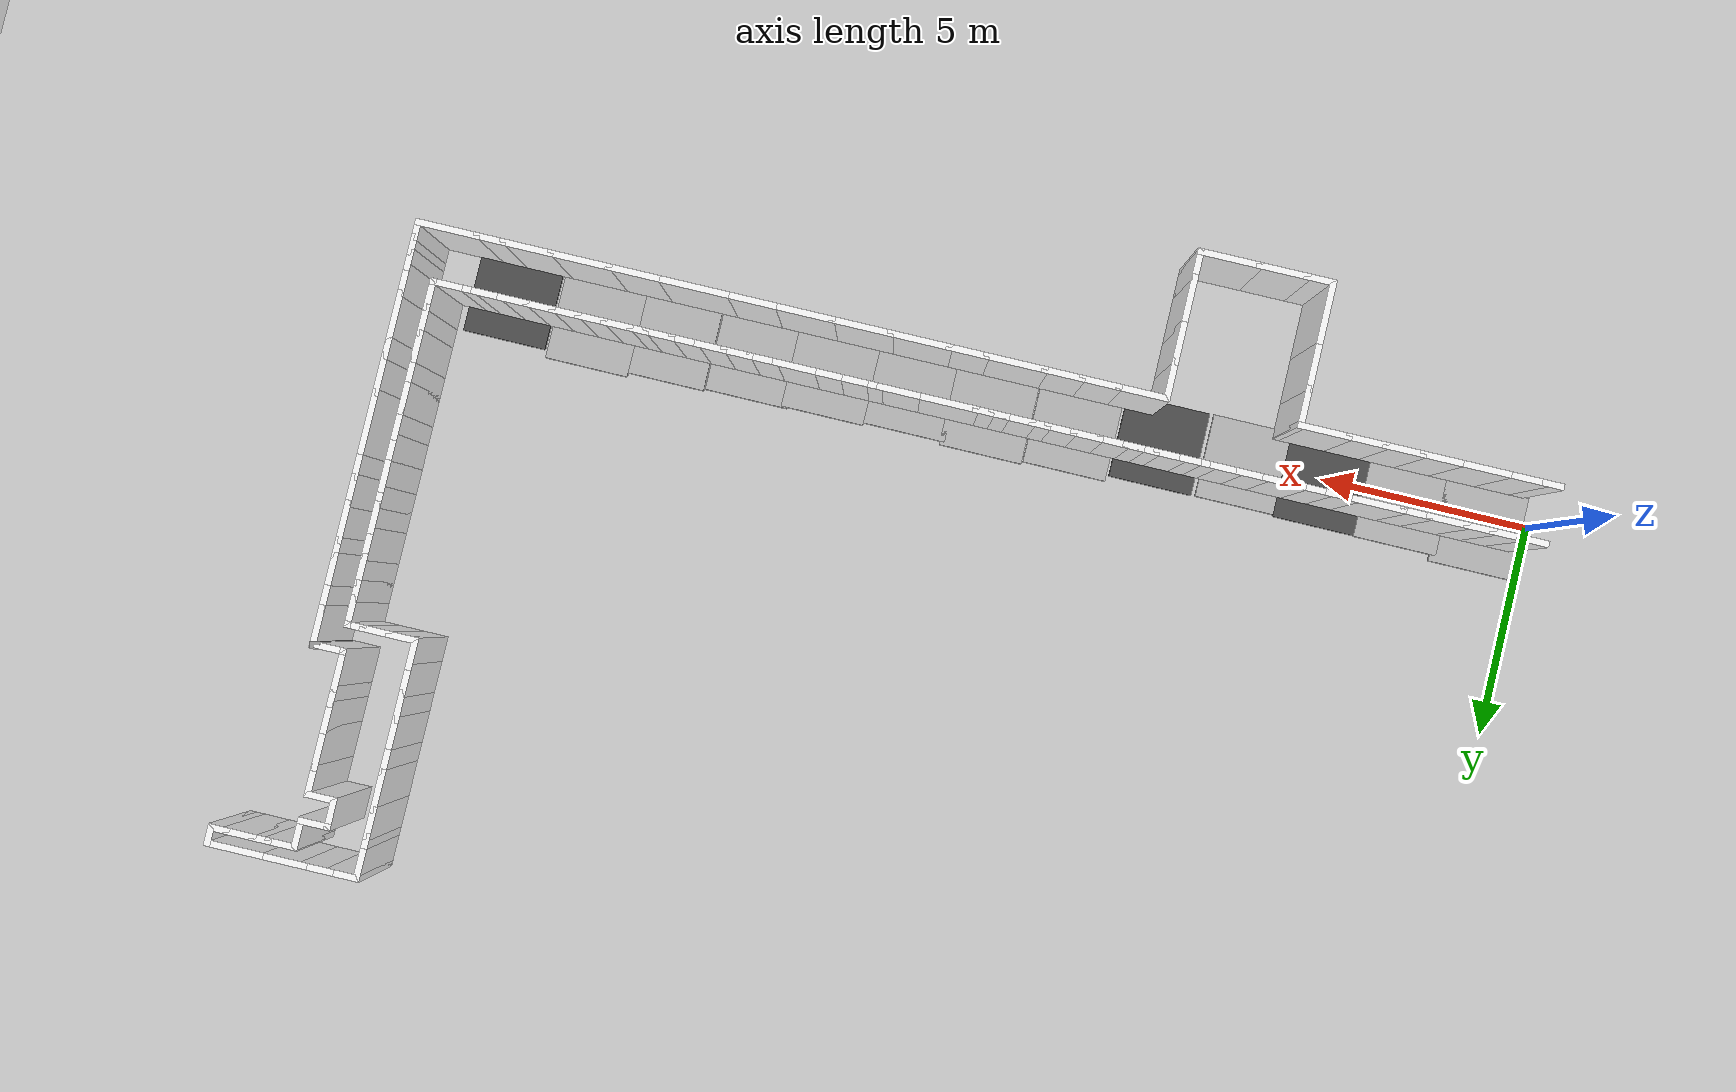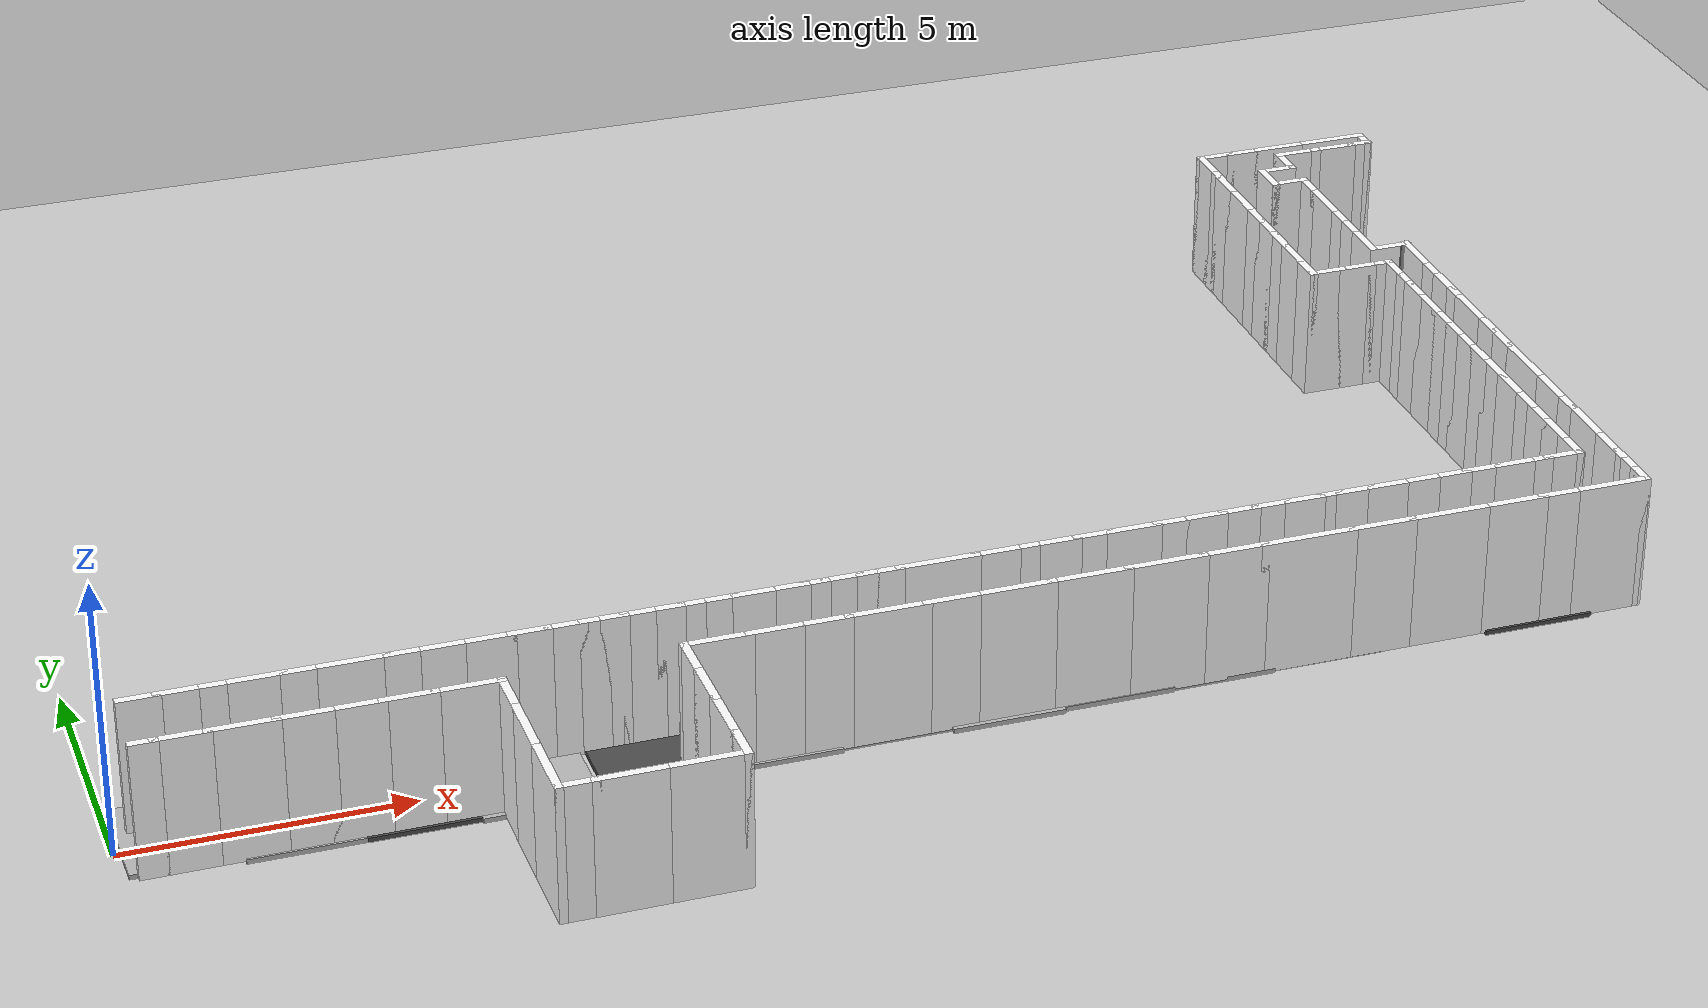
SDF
<sdf version="1.6">
 <world name="default">
  <model name="ground_plane">
   <static>1</static>
   <link name="link">
    <collision name="collision">
     <geometry><plane><normal>0 0 1</normal><size>100 100</size></plane></geometry>
     <surface><friction><ode><mu>100</mu><mu2>50</mu2></ode></friction></surface>
    </collision>
    <visual name="visual">
     <cast_shadows>0</cast_shadows>
     <geometry><plane><normal>0 0 1</normal><size>100 100</size></plane></geometry>
     <material>
      <script><uri>file://media/materials/scripts/gazebo.material</uri><name>Gazebo/Grey</name></script>
     </material>
    </visual>
   </link>
  </model>
  <light name="sun" type="directional">
   <pose>0 0 10 0 -0 0</pose>
   <diffuse>0.8 0.8 0.8 1</diffuse>
   <specular>0.1 0.1 0.1 1</specular>
   <attenuation>
    <range>1000</range>
    <constant>0.9</constant>
    <linear>0.01</linear>
    <quadratic>0.001</quadratic>
   </attenuation>
   <direction>-0.5 0.5 -1</direction>
  </light>
  <plugin name="ros_interface_plugin" filename="librotors_gazebo_ros_interface_plugin.so"/>
  <spherical_coordinates>
   <surface_model>EARTH_WGS84</surface_model>
   <latitude_deg>47.3667</latitude_deg>
   <longitude_deg>8.55</longitude_deg>
   <elevation>500</elevation>
   <heading_deg>0</heading_deg>
  </spherical_coordinates>
  <physics name="default_physics" default="0" type="ode">
   <ode>
    <solver>
     <type>quick</type>
     <iters>1000</iters>
     <sor>1.3</sor>
     <use_dynamic_moi_rescaling>0</use_dynamic_moi_rescaling>
    </solver>
    <constraints>
     <cfm>0</cfm>
     <erp>0.2</erp>
     <contact_max_correcting_vel>100</contact_max_correcting_vel>
     <contact_surface_layer>0.001</contact_surface_layer>
    </constraints>
   </ode>
   <max_step_size>0.01</max_step_size>
   <real_time_factor>1</real_time_factor>
   <real_time_update_rate>100</real_time_update_rate>
  </physics>
  <gravity>0 0 -9.8</gravity>
  <magnetic_field>6e-06 2.3e-05 -4.2e-05</magnetic_field>
  <atmosphere type="adiabatic"/>
  <scene><ambient>0.4 0.4 0.4 1</ambient><background>0.7 0.7 0.7 1</background><shadows>1</shadows></scene>
  <model name="hightextured">
   <pose>14.0303 4.95039 0 0 0 -1.56774</pose>
   <link name="Wall_0">
    <collision name="Wall_0_Collision">
     <geometry><box><size>1.5 0.15 2.5</size></box></geometry>
     <pose>0 0 1.25 0 -0 0</pose>
    </collision>
    <visual name="Wall_0_Visual">
     <pose>0 0 1.25 0 -0 0</pose>
     <geometry><box><size>1.5 0.15 2.5</size></box></geometry>
     <material>
      <script><uri>file://media/materials/scripts/gazebo.material</uri><name>Gazebo/Texture11</name></script>
      <ambient>1 1 1 1</ambient>
     </material>
    </visual>
    <pose>-8.96206 13.0517 0 0 0 -1.5708</pose>
   </link>
   <link name="Wall_1">
    <collision name="Wall_1_Collision">
     <geometry><box><size>1 0.15 2.5</size></box></geometry>
     <pose>0 0 1.25 0 -0 0</pose>
    </collision>
    <visual name="Wall_1_Visual">
     <pose>0 0 1.25 0 -0 0</pose>
     <geometry><box><size>1 0.15 2.5</size></box></geometry>
     <material>
      <script><uri>file://media/materials/scripts/gazebo.material</uri><name>Gazebo/Texture1</name></script>
      <ambient>1 1 1 1</ambient>
     </material>
    </visual>
    <pose>-8.96206 11.9517 0 0 0 -1.5708</pose>
   </link>
   <link name="Wall_10">
    <collision name="Wall_10_Collision">
     <geometry><box><size>0.75 0.15 2.5</size></box></geometry>
     <pose>0 0 1.25 0 -0 0</pose>
    </collision>
    <visual name="Wall_10_Visual">
     <pose>0 0 1.25 0 -0 0</pose>
     <geometry><box><size>0.75 0.15 2.5</size></box></geometry>
     <material>
      <script><uri>file://media/materials/scripts/gazebo.material</uri><name>Gazebo/Texture2</name></script>
      <ambient>1 1 1 1</ambient>
     </material>
    </visual>
    <pose>-5.06206 10.3267 0 0 -0 0</pose>
   </link>
   <link name="Wall_100">
    <collision name="Wall_100_Collision">
     <geometry><box><size>0.75 0.15 2.5</size></box></geometry>
     <pose>0 0 1.25 0 -0 0</pose>
    </collision>
    <visual name="Wall_100_Visual">
     <pose>0 0 1.25 0 -0 0</pose>
     <geometry><box><size>0.75 0.15 2.5</size></box></geometry>
     <material>
      <script><uri>file://media/materials/scripts/gazebo.material</uri><name>Gazebo/Texture3</name></script>
      <ambient>1 1 1 1</ambient>
     </material>
    </visual>
    <pose>4.33794 -5.0733 0 0 0 -1.5708</pose>
   </link>
   <link name="Wall_101">
    <collision name="Wall_101_Collision">
     <geometry><box><size>0.5 0.15 2.5</size></box></geometry>
     <pose>0 0 1.25 0 -0 0</pose>
    </collision>
    <visual name="Wall_101_Visual">
     <pose>0 0 1.25 0 -0 0</pose>
     <geometry><box><size>0.5 0.15 2.5</size></box></geometry>
     <material>
      <script><uri>file://media/materials/scripts/gazebo.material</uri><name>Gazebo/Texture11</name></script>
      <ambient>1 1 1 1</ambient>
     </material>
    </visual>
    <pose>4.33794 -5.5483 0 0 0 -1.5708</pose>
   </link>
   <link name="Wall_102">
    <collision name="Wall_102_Collision">
     <geometry><box><size>0.5 0.15 2.5</size></box></geometry>
     <pose>0 0 1.25 0 -0 0</pose>
    </collision>
    <visual name="Wall_102_Visual">
     <pose>0 0 1.25 0 -0 0</pose>
     <geometry><box><size>0.5 0.15 2.5</size></box></geometry>
     <material>
      <script><uri>file://media/materials/scripts/gazebo.material</uri><name>Gazebo/Texture4</name></script>
      <ambient>1 1 1 1</ambient>
     </material>
    </visual>
    <pose>4.33794 -5.8983 0 0 0 -1.5708</pose>
   </link>
   <link name="Wall_103">
    <collision name="Wall_103_Collision">
     <geometry><box><size>0.75 0.15 2.5</size></box></geometry>
     <pose>0 0 1.25 0 -0 0</pose>
    </collision>
    <visual name="Wall_103_Visual">
     <pose>0 0 1.25 0 -0 0</pose>
     <geometry><box><size>0.75 0.15 2.5</size></box></geometry>
     <material>
      <script><uri>file://media/materials/scripts/gazebo.material</uri><name>Gazebo/Texture5</name></script>
      <ambient>1 1 1 1</ambient>
     </material>
    </visual>
    <pose>4.33794 -6.3733 0 0 0 -1.5708</pose>
   </link>
   <link name="Wall_104">
    <collision name="Wall_104_Collision">
     <geometry><box><size>0.75 0.15 2.5</size></box></geometry>
     <pose>0 0 1.25 0 -0 0</pose>
    </collision>
    <visual name="Wall_104_Visual">
     <pose>0 0 1.25 0 -0 0</pose>
     <geometry><box><size>0.75 0.15 2.5</size></box></geometry>
     <material>
      <script><uri>file://media/materials/scripts/gazebo.material</uri><name>Gazebo/Texture6</name></script>
      <ambient>1 1 1 1</ambient>
     </material>
    </visual>
    <pose>4.33794 -6.9733 0 0 0 -1.5708</pose>
   </link>
   <link name="Wall_105">
    <collision name="Wall_105_Collision">
     <geometry><box><size>1 0.15 2.5</size></box></geometry>
     <pose>0 0 1.25 0 -0 0</pose>
    </collision>
    <visual name="Wall_105_Visual">
     <pose>0 0 1.25 0 -0 0</pose>
     <geometry><box><size>1 0.15 2.5</size></box></geometry>
     <material>
      <script><uri>file://media/materials/scripts/gazebo.material</uri><name>Gazebo/Texture7</name></script>
      <ambient>1 1 1 1</ambient>
     </material>
    </visual>
    <pose>4.33794 -7.6983 0 0 0 -1.5708</pose>
   </link>
   <link name="Wall_106">
    <collision name="Wall_106_Collision">
     <geometry><box><size>0.75 0.15 2.5</size></box></geometry>
     <pose>0 0 1.25 0 -0 0</pose>
    </collision>
    <visual name="Wall_106_Visual">
     <pose>0 0 1.25 0 -0 0</pose>
     <geometry><box><size>0.75 0.15 2.5</size></box></geometry>
     <material>
      <script><uri>file://media/materials/scripts/gazebo.material</uri><name>Gazebo/Texture8</name></script>
      <ambient>1 1 1 1</ambient>
     </material>
    </visual>
    <pose>4.33794 -8.4233 0 0 0 -1.5708</pose>
   </link>
   <link name="Wall_107">
    <collision name="Wall_107_Collision">
     <geometry><box><size>0.75 0.15 2.5</size></box></geometry>
     <pose>0 0 1.25 0 -0 0</pose>
    </collision>
    <visual name="Wall_107_Visual">
     <pose>0 0 1.25 0 -0 0</pose>
     <geometry><box><size>0.75 0.15 2.5</size></box></geometry>
     <material>
      <script><uri>file://media/materials/scripts/gazebo.material</uri><name>Gazebo/Texture9</name></script>
      <ambient>1 1 1 1</ambient>
     </material>
    </visual>
    <pose>4.33794 -9.0233 0 0 0 -1.5708</pose>
   </link>
   <link name="Wall_108">
    <collision name="Wall_108_Collision">
     <geometry><box><size>1.25 0.15 2.5</size></box></geometry>
     <pose>0 0 1.25 0 -0 0</pose>
    </collision>
    <visual name="Wall_108_Visual">
     <pose>0 0 1.25 0 -0 0</pose>
     <geometry><box><size>1.25 0.15 2.5</size></box></geometry>
     <material>
      <script><uri>file://media/materials/scripts/gazebo.material</uri><name>Gazebo/Texture10</name></script>
      <ambient>1 1 1 1</ambient>
     </material>
    </visual>
    <pose>4.33794 -9.8733 0 0 0 -1.5708</pose>
   </link>
   <link name="Wall_109">
    <collision name="Wall_109_Collision">
     <geometry><box><size>0.75 0.15 2.5</size></box></geometry>
     <pose>0 0 1.25 0 -0 0</pose>
    </collision>
    <visual name="Wall_109_Visual">
     <pose>0 0 1.25 0 -0 0</pose>
     <geometry><box><size>0.75 0.15 2.5</size></box></geometry>
     <material>
      <script><uri>file://media/materials/scripts/gazebo.material</uri><name>Gazebo/Texture11</name></script>
      <ambient>1 1 1 1</ambient>
     </material>
    </visual>
    <pose>4.33794 -10.7233 0 0 0 -1.5708</pose>
   </link>
   <link name="Wall_11">
    <collision name="Wall_11_Collision">
     <geometry><box><size>0.75 0.15 2.5</size></box></geometry>
     <pose>0 0 1.25 0 -0 0</pose>
    </collision>
    <visual name="Wall_11_Visual">
     <pose>0 0 1.25 0 -0 0</pose>
     <geometry><box><size>0.75 0.15 2.5</size></box></geometry>
     <material>
      <script><uri>file://media/materials/scripts/gazebo.material</uri><name>Gazebo/Texture12</name></script>
      <ambient>1 1 1 1</ambient>
     </material>
    </visual>
    <pose>-4.46206 10.3267 0 0 -0 0</pose>
   </link>
   <link name="Wall_110">
    <collision name="Wall_110_Collision">
     <geometry><box><size>1 0.15 2.5</size></box></geometry>
     <pose>0 0 1.25 0 -0 0</pose>
    </collision>
    <visual name="Wall_110_Visual">
     <pose>0 0 1.25 0 -0 0</pose>
     <geometry><box><size>1 0.15 2.5</size></box></geometry>
     <material>
      <script><uri>file://media/materials/scripts/gazebo.material</uri><name>Gazebo/Texture13</name></script>
      <ambient>1 1 1 1</ambient>
     </material>
    </visual>
    <pose>4.33794 -11.4483 0 0 0 -1.5708</pose>
   </link>
   <link name="Wall_111">
    <collision name="Wall_111_Collision">
     <geometry><box><size>0.75 0.15 2.5</size></box></geometry>
     <pose>0 0 1.25 0 -0 0</pose>
    </collision>
    <visual name="Wall_111_Visual">
     <pose>0 0 1.25 0 -0 0</pose>
     <geometry><box><size>0.75 0.15 2.5</size></box></geometry>
     <material>
      <script><uri>file://media/materials/scripts/gazebo.material</uri><name>Gazebo/Texture14</name></script>
      <ambient>1 1 1 1</ambient>
     </material>
    </visual>
    <pose>4.33794 -12.1733 0 0 0 -1.5708</pose>
   </link>
   <link name="Wall_112">
    <collision name="Wall_112_Collision">
     <geometry><box><size>0.75 0.15 2.5</size></box></geometry>
     <pose>0 0 1.25 0 -0 0</pose>
    </collision>
    <visual name="Wall_112_Visual">
     <pose>0 0 1.25 0 -0 0</pose>
     <geometry><box><size>0.75 0.15 2.5</size></box></geometry>
     <material>
      <script><uri>file://media/materials/scripts/gazebo.material</uri><name>Gazebo/Texture15</name></script>
      <ambient>1 1 1 1</ambient>
     </material>
    </visual>
    <pose>4.33794 -12.7733 0 0 0 -1.5708</pose>
   </link>
   <link name="Wall_113">
    <collision name="Wall_113_Collision">
     <geometry><box><size>0.75 0.15 2.5</size></box></geometry>
     <pose>0 0 1.25 0 -0 0</pose>
    </collision>
    <visual name="Wall_113_Visual">
     <pose>0 0 1.25 0 -0 0</pose>
     <geometry><box><size>0.75 0.15 2.5</size></box></geometry>
     <material>
      <script><uri>file://media/materials/scripts/gazebo.material</uri><name>Gazebo/Texture16</name></script>
      <ambient>1 1 1 1</ambient>
     </material>
    </visual>
    <pose>4.33794 -13.3733 0 0 0 -1.5708</pose>
   </link>
   <link name="Wall_116">
    <collision name="Wall_116_Collision">
     <geometry><box><size>0.5 0.15 2.5</size></box></geometry>
     <pose>0 0 1.25 0 -0 0</pose>
    </collision>
    <visual name="Wall_116_Visual">
     <pose>0 0 1.25 0 -0 0</pose>
     <geometry><box><size>0.5 0.15 2.5</size></box></geometry>
     <material>
      <script><uri>file://media/materials/scripts/gazebo.material</uri><name>Gazebo/Texture17</name></script>
      <ambient>1 1 1 1</ambient>
     </material>
    </visual>
    <pose>4.68706 12.5233 0 0 -0 0</pose>
   </link>
   <link name="Wall_117">
    <collision name="Wall_117_Collision">
     <geometry><box><size>0.5 0.15 2.5</size></box></geometry>
     <pose>0 0 1.25 0 -0 0</pose>
    </collision>
    <visual name="Wall_117_Visual">
     <pose>0 0 1.25 0 -0 0</pose>
     <geometry><box><size>0.5 0.15 2.5</size></box></geometry>
     <material>
      <script><uri>file://media/materials/scripts/gazebo.material</uri><name>Gazebo/Texture18</name></script>
      <ambient>1 1 1 1</ambient>
     </material>
    </visual>
    <pose>5.03706 12.5233 0 0 -0 0</pose>
   </link>
   <link name="Wall_118">
    <collision name="Wall_118_Collision">
     <geometry><box><size>0.5 0.15 2.5</size></box></geometry>
     <pose>0 0 1.25 0 -0 0</pose>
    </collision>
    <visual name="Wall_118_Visual">
     <pose>0 0 1.25 0 -0 0</pose>
     <geometry><box><size>0.5 0.15 2.5</size></box></geometry>
     <material>
      <script><uri>file://media/materials/scripts/gazebo.material</uri><name>Gazebo/Texture18</name></script>
      <ambient>1 1 1 1</ambient>
     </material>
    </visual>
    <pose>5.38706 12.5233 0 0 -0 0</pose>
   </link>
   <link name="Wall_119">
    <collision name="Wall_119_Collision">
     <geometry><box><size>1.5 0.15 2.5</size></box></geometry>
     <pose>0 0 1.25 0 -0 0</pose>
    </collision>
    <visual name="Wall_119_Visual">
     <pose>0 0 1.25 0 -0 0</pose>
     <geometry><box><size>1.5 0.15 2.5</size></box></geometry>
     <material>
      <script><uri>file://media/materials/scripts/gazebo.material</uri><name>Gazebo/Texture17</name></script>
      <ambient>1 1 1 1</ambient>
     </material>
    </visual>
    <pose>5.56206 11.8483 0 0 0 -1.5708</pose>
   </link>
   <link name="Wall_12">
    <collision name="Wall_12_Collision">
     <geometry><box><size>0.75 0.15 2.5</size></box></geometry>
     <pose>0 0 1.25 0 -0 0</pose>
    </collision>
    <visual name="Wall_12_Visual">
     <pose>0 0 1.25 0 -0 0</pose>
     <geometry><box><size>0.75 0.15 2.5</size></box></geometry>
     <material>
      <script><uri>file://media/materials/scripts/gazebo.material</uri><name>Gazebo/Texture16</name></script>
      <ambient>1 1 1 1</ambient>
     </material>
    </visual>
    <pose>-3.86206 10.3267 0 0 -0 0</pose>
   </link>
   <link name="Wall_120">
    <collision name="Wall_120_Collision">
     <geometry><box><size>0.75 0.15 2.5</size></box></geometry>
     <pose>0 0 1.25 0 -0 0</pose>
    </collision>
    <visual name="Wall_120_Visual">
     <pose>0 0 1.25 0 -0 0</pose>
     <geometry><box><size>0.75 0.15 2.5</size></box></geometry>
     <material>
      <script><uri>file://media/materials/scripts/gazebo.material</uri><name>Gazebo/Texture15</name></script>
      <ambient>1 1 1 1</ambient>
     </material>
    </visual>
    <pose>5.56206 10.8733 0 0 0 -1.5708</pose>
   </link>
   <link name="Wall_121">
    <collision name="Wall_121_Collision">
     <geometry><box><size>1.25 0.15 2.5</size></box></geometry>
     <pose>0 0 1.25 0 -0 0</pose>
    </collision>
    <visual name="Wall_121_Visual">
     <pose>0 0 1.25 0 -0 0</pose>
     <geometry><box><size>1.25 0.15 2.5</size></box></geometry>
     <material>
      <script><uri>file://media/materials/scripts/gazebo.material</uri><name>Gazebo/Texture14</name></script>
      <ambient>1 1 1 1</ambient>
     </material>
    </visual>
    <pose>5.56206 10.0233 0 0 0 -1.5708</pose>
   </link>
   <link name="Wall_122">
    <collision name="Wall_122_Collision">
     <geometry><box><size>1.5 0.15 2.5</size></box></geometry>
     <pose>0 0 1.25 0 -0 0</pose>
    </collision>
    <visual name="Wall_122_Visual">
     <pose>0 0 1.25 0 -0 0</pose>
     <geometry><box><size>1.5 0.15 2.5</size></box></geometry>
     <material>
      <script><uri>file://media/materials/scripts/gazebo.material</uri><name>Gazebo/Texture13</name></script>
      <ambient>1 1 1 1</ambient>
     </material>
    </visual>
    <pose>5.56206 8.7983 0 0 0 -1.5708</pose>
   </link>
   <link name="Wall_123">
    <collision name="Wall_123_Collision">
     <geometry><box><size>1.25 0.15 2.5</size></box></geometry>
     <pose>0 0 1.25 0 -0 0</pose>
    </collision>
    <visual name="Wall_123_Visual">
     <pose>0 0 1.25 0 -0 0</pose>
     <geometry><box><size>1.25 0.15 2.5</size></box></geometry>
     <material>
      <script><uri>file://media/materials/scripts/gazebo.material</uri><name>Gazebo/Texture12</name></script>
      <ambient>1 1 1 1</ambient>
     </material>
    </visual>
    <pose>5.56206 7.5733 0 0 0 -1.5708</pose>
   </link>
   <link name="Wall_124">
    <collision name="Wall_124_Collision">
     <geometry><box><size>1.75 0.15 2.5</size></box></geometry>
     <pose>0 0 1.25 0 -0 0</pose>
    </collision>
    <visual name="Wall_124_Visual">
     <pose>0 0 1.25 0 -0 0</pose>
     <geometry><box><size>1.75 0.15 2.5</size></box></geometry>
     <material>
      <script><uri>file://media/materials/scripts/gazebo.material</uri><name>Gazebo/Texture11</name></script>
      <ambient>1 1 1 1</ambient>
     </material>
    </visual>
    <pose>5.56206 6.2233 0 0 0 -1.5708</pose>
   </link>
   <link name="Wall_125">
    <collision name="Wall_125_Collision">
     <geometry><box><size>1.25 0.15 2.5</size></box></geometry>
     <pose>0 0 1.25 0 -0 0</pose>
    </collision>
    <visual name="Wall_125_Visual">
     <pose>0 0 1.25 0 -0 0</pose>
     <geometry><box><size>1.25 0.15 2.5</size></box></geometry>
     <material>
      <script><uri>file://media/materials/scripts/gazebo.material</uri><name>Gazebo/Texture10</name></script>
      <ambient>1 1 1 1</ambient>
     </material>
    </visual>
    <pose>5.56206 4.8733 0 0 0 -1.5708</pose>
   </link>
   <link name="Wall_126">
    <collision name="Wall_126_Collision">
     <geometry><box><size>1.5 0.15 2.5</size></box></geometry>
     <pose>0 0 1.25 0 -0 0</pose>
    </collision>
    <visual name="Wall_126_Visual">
     <pose>0 0 1.25 0 -0 0</pose>
     <geometry><box><size>1.5 0.15 2.5</size></box></geometry>
     <material>
      <script><uri>file://media/materials/scripts/gazebo.material</uri><name>Gazebo/Texture9</name></script>
      <ambient>1 1 1 1</ambient>
     </material>
    </visual>
    <pose>5.56206 3.6483 0 0 0 -1.5708</pose>
   </link>
   <link name="Wall_127">
    <collision name="Wall_127_Collision">
     <geometry><box><size>1.5 0.15 2.5</size></box></geometry>
     <pose>0 0 1.25 0 -0 0</pose>
    </collision>
    <visual name="Wall_127_Visual">
     <pose>0 0 1.25 0 -0 0</pose>
     <geometry><box><size>1.5 0.15 2.5</size></box></geometry>
     <material>
      <script><uri>file://media/materials/scripts/gazebo.material</uri><name>Gazebo/Texture8</name></script>
      <ambient>1 1 1 1</ambient>
     </material>
    </visual>
    <pose>5.56206 2.2983 0 0 0 -1.5708</pose>
   </link>
   <link name="Wall_128">
    <collision name="Wall_128_Collision">
     <geometry><box><size>1.5 0.15 2.5</size></box></geometry>
     <pose>0 0 1.25 0 -0 0</pose>
    </collision>
    <visual name="Wall_128_Visual">
     <pose>0 0 1.25 0 -0 0</pose>
     <geometry><box><size>1.5 0.15 2.5</size></box></geometry>
     <material>
      <script><uri>file://media/materials/scripts/gazebo.material</uri><name>Gazebo/Texture7</name></script>
      <ambient>1 1 1 1</ambient>
     </material>
    </visual>
    <pose>5.56206 0.948296 0 0 0 -1.5708</pose>
   </link>
   <link name="Wall_129">
    <collision name="Wall_129_Collision">
     <geometry><box><size>1 0.15 2.5</size></box></geometry>
     <pose>0 0 1.25 0 -0 0</pose>
    </collision>
    <visual name="Wall_129_Visual">
     <pose>0 0 1.25 0 -0 0</pose>
     <geometry><box><size>1 0.15 2.5</size></box></geometry>
     <material>
      <script><uri>file://media/materials/scripts/gazebo.material</uri><name>Gazebo/Texture6</name></script>
      <ambient>1 1 1 1</ambient>
     </material>
    </visual>
    <pose>5.56206 -0.151704 0 0 0 -1.5708</pose>
   </link>
   <link name="Wall_13">
    <collision name="Wall_13_Collision">
     <geometry><box><size>0.75 0.15 2.5</size></box></geometry>
     <pose>0 0 1.25 0 -0 0</pose>
    </collision>
    <visual name="Wall_13_Visual">
     <pose>0 0 1.25 0 -0 0</pose>
     <geometry><box><size>0.75 0.15 2.5</size></box></geometry>
     <material>
      <script><uri>file://media/materials/scripts/gazebo.material</uri><name>Gazebo/Texture5</name></script>
      <ambient>1 1 1 1</ambient>
     </material>
    </visual>
    <pose>-3.56206 10.6267 0 0 -0 1.5708</pose>
   </link>
   <link name="Wall_130">
    <collision name="Wall_130_Collision">
     <geometry><box><size>1.5 0.15 2.5</size></box></geometry>
     <pose>0 0 1.25 0 -0 0</pose>
    </collision>
    <visual name="Wall_130_Visual">
     <pose>0 0 1.25 0 -0 0</pose>
     <geometry><box><size>1.5 0.15 2.5</size></box></geometry>
     <material>
      <script><uri>file://media/materials/scripts/gazebo.material</uri><name>Gazebo/Texture4</name></script>
      <ambient>1 1 1 1</ambient>
     </material>
    </visual>
    <pose>5.56206 -1.2517 0 0 0 -1.5708</pose>
   </link>
   <link name="Wall_131">
    <collision name="Wall_131_Collision">
     <geometry><box><size>1 0.15 2.5</size></box></geometry>
     <pose>0 0 1.25 0 -0 0</pose>
    </collision>
    <visual name="Wall_131_Visual">
     <pose>0 0 1.25 0 -0 0</pose>
     <geometry><box><size>1 0.15 2.5</size></box></geometry>
     <material>
      <script><uri>file://media/materials/scripts/gazebo.material</uri><name>Gazebo/Texture3</name></script>
      <ambient>1 1 1 1</ambient>
     </material>
    </visual>
    <pose>5.56206 -2.3517 0 0 0 -1.5708</pose>
   </link>
   <link name="Wall_132">
    <collision name="Wall_132_Collision">
     <geometry><box><size>1 0.15 2.5</size></box></geometry>
     <pose>0 0 1.25 0 -0 0</pose>
    </collision>
    <visual name="Wall_132_Visual">
     <pose>0 0 1.25 0 -0 0</pose>
     <geometry><box><size>1 0.15 2.5</size></box></geometry>
     <material>
      <script><uri>file://media/materials/scripts/gazebo.material</uri><name>Gazebo/Texture2</name></script>
      <ambient>1 1 1 1</ambient>
     </material>
    </visual>
    <pose>5.56206 -3.2017 0 0 0 -1.5708</pose>
   </link>
   <link name="Wall_133">
    <collision name="Wall_133_Collision">
     <geometry><box><size>1.25 0.15 2.5</size></box></geometry>
     <pose>0 0 1.25 0 -0 0</pose>
    </collision>
    <visual name="Wall_133_Visual">
     <pose>0 0 1.25 0 -0 0</pose>
     <geometry><box><size>1.25 0.15 2.5</size></box></geometry>
     <material>
      <script><uri>file://media/materials/scripts/gazebo.material</uri><name>Gazebo/Texture1</name></script>
      <ambient>1 1 1 1</ambient>
     </material>
    </visual>
    <pose>5.56206 -4.1767 0 0 0 -1.5708</pose>
   </link>
   <link name="Wall_136">
    <collision name="Wall_136_Collision">
     <geometry><box><size>1 0.15 2.5</size></box></geometry>
     <pose>0 0 1.25 0 -0 0</pose>
    </collision>
    <visual name="Wall_136_Visual">
     <pose>0 0 1.25 0 -0 0</pose>
     <geometry><box><size>1 0.15 2.5</size></box></geometry>
     <material>
      <script><uri>file://media/materials/scripts/gazebo.material</uri><name>Gazebo/Texture2</name></script>
      <ambient>1 1 1 1</ambient>
     </material>
    </visual>
    <pose>5.98706 -4.7267 0 0 -0 0</pose>
   </link>
   <link name="Wall_137">
    <collision name="Wall_137_Collision">
     <geometry><box><size>1 0.15 2.5</size></box></geometry>
     <pose>0 0 1.25 0 -0 0</pose>
    </collision>
    <visual name="Wall_137_Visual">
     <pose>0 0 1.25 0 -0 0</pose>
     <geometry><box><size>1 0.15 2.5</size></box></geometry>
     <material>
      <script><uri>file://media/materials/scripts/gazebo.material</uri><name>Gazebo/Texture3</name></script>
      <ambient>1 1 1 1</ambient>
     </material>
    </visual>
    <pose>6.83706 -4.7267 0 0 -0 0</pose>
   </link>
   <link name="Wall_138">
    <collision name="Wall_138_Collision">
     <geometry><box><size>1.25 0.15 2.5</size></box></geometry>
     <pose>0 0 1.25 0 -0 0</pose>
    </collision>
    <visual name="Wall_138_Visual">
     <pose>0 0 1.25 0 -0 0</pose>
     <geometry><box><size>1.25 0.15 2.5</size></box></geometry>
     <material>
      <script><uri>file://media/materials/scripts/gazebo.material</uri><name>Gazebo/Texture4</name></script>
      <ambient>1 1 1 1</ambient>
     </material>
    </visual>
    <pose>7.81206 -4.7267 0 0 -0 0</pose>
   </link>
   <link name="Wall_139">
    <collision name="Wall_139_Collision">
     <geometry><box><size>0.75 0.15 2.5</size></box></geometry>
     <pose>0 0 1.25 0 -0 0</pose>
    </collision>
    <visual name="Wall_139_Visual">
     <pose>0 0 1.25 0 -0 0</pose>
     <geometry><box><size>0.75 0.15 2.5</size></box></geometry>
     <material>
      <script><uri>file://media/materials/scripts/gazebo.material</uri><name>Gazebo/Texture5</name></script>
      <ambient>1 1 1 1</ambient>
     </material>
    </visual>
    <pose>8.66206 -4.7267 0 0 -0 0</pose>
   </link>
   <link name="Wall_14">
    <collision name="Wall_14_Collision">
     <geometry><box><size>0.75 0.15 2.5</size></box></geometry>
     <pose>0 0 1.25 0 -0 0</pose>
    </collision>
    <visual name="Wall_14_Visual">
     <pose>0 0 1.25 0 -0 0</pose>
     <geometry><box><size>0.75 0.15 2.5</size></box></geometry>
     <material>
      <script><uri>file://media/materials/scripts/gazebo.material</uri><name>Gazebo/Texture6</name></script>
      <ambient>1 1 1 1</ambient>
     </material>
    </visual>
    <pose>-3.56206 11.2267 0 0 -0 1.5708</pose>
   </link>
   <link name="Wall_140">
    <collision name="Wall_140_Collision">
     <geometry><box><size>1.5 0.15 2.5</size></box></geometry>
     <pose>0 0 1.25 0 -0 0</pose>
    </collision>
    <visual name="Wall_140_Visual">
     <pose>0 0 1.25 0 -0 0</pose>
     <geometry><box><size>1.5 0.15 2.5</size></box></geometry>
     <material>
      <script><uri>file://media/materials/scripts/gazebo.material</uri><name>Gazebo/Texture7</name></script>
      <ambient>1 1 1 1</ambient>
     </material>
    </visual>
    <pose>8.96206 -5.4017 0 0 0 -1.5708</pose>
   </link>
   <link name="Wall_141">
    <collision name="Wall_141_Collision">
     <geometry><box><size>1.25 0.15 2.5</size></box></geometry>
     <pose>0 0 1.25 0 -0 0</pose>
    </collision>
    <visual name="Wall_141_Visual">
     <pose>0 0 1.25 0 -0 0</pose>
     <geometry><box><size>1.25 0.15 2.5</size></box></geometry>
     <material>
      <script><uri>file://media/materials/scripts/gazebo.material</uri><name>Gazebo/Texture8</name></script>
      <ambient>1 1 1 1</ambient>
     </material>
    </visual>
    <pose>8.96206 -6.6267 0 0 0 -1.5708</pose>
   </link>
   <link name="Wall_142">
    <collision name="Wall_142_Collision">
     <geometry><box><size>0.75 0.15 2.5</size></box></geometry>
     <pose>0 0 1.25 0 -0 0</pose>
    </collision>
    <visual name="Wall_142_Visual">
     <pose>0 0 1.25 0 -0 0</pose>
     <geometry><box><size>0.75 0.15 2.5</size></box></geometry>
     <material>
      <script><uri>file://media/materials/scripts/gazebo.material</uri><name>Gazebo/Texture9</name></script>
      <ambient>1 1 1 1</ambient>
     </material>
    </visual>
    <pose>8.96206 -7.4767 0 0 0 -1.5708</pose>
   </link>
   <link name="Wall_143">
    <collision name="Wall_143_Collision">
     <geometry><box><size>1.5 0.15 2.5</size></box></geometry>
     <pose>0 0 1.25 0 -0 0</pose>
    </collision>
    <visual name="Wall_143_Visual">
     <pose>0 0 1.25 0 -0 0</pose>
     <geometry><box><size>1.5 0.15 2.5</size></box></geometry>
     <material>
      <script><uri>file://media/materials/scripts/gazebo.material</uri><name>Gazebo/Texture10</name></script>
      <ambient>1 1 1 1</ambient>
     </material>
    </visual>
    <pose>8.28706 -7.7767 0 0 -0 3.14159</pose>
   </link>
   <link name="Wall_144">
    <collision name="Wall_144_Collision">
     <geometry><box><size>1.25 0.15 2.5</size></box></geometry>
     <pose>0 0 1.25 0 -0 0</pose>
    </collision>
    <visual name="Wall_144_Visual">
     <pose>0 0 1.25 0 -0 0</pose>
     <geometry><box><size>1.25 0.15 2.5</size></box></geometry>
     <material>
      <script><uri>file://media/materials/scripts/gazebo.material</uri><name>Gazebo/Texture11</name></script>
      <ambient>1 1 1 1</ambient>
     </material>
    </visual>
    <pose>7.06206 -7.7767 0 0 -0 3.14159</pose>
   </link>
   <link name="Wall_147">
    <collision name="Wall_147_Collision">
     <geometry><box><size>1 0.15 2.5</size></box></geometry>
     <pose>0 0 1.25 0 -0 0</pose>
    </collision>
    <visual name="Wall_147_Visual">
     <pose>0 0 1.25 0 -0 0</pose>
     <geometry><box><size>1 0.15 2.5</size></box></geometry>
     <material>
      <script><uri>file://media/materials/scripts/gazebo.material</uri><name>Gazebo/Texture12</name></script>
      <ambient>1 1 1 1</ambient>
     </material>
    </visual>
    <pose>6.08706 -7.7767 0 0 -0 3.14159</pose>
   </link>
   <link name="Wall_15">
    <collision name="Wall_15_Collision">
     <geometry><box><size>0.5 0.15 2.5</size></box></geometry>
     <pose>0 0 1.25 0 -0 0</pose>
    </collision>
    <visual name="Wall_15_Visual">
     <pose>0 0 1.25 0 -0 0</pose>
     <geometry><box><size>0.5 0.15 2.5</size></box></geometry>
     <material>
      <script><uri>file://media/materials/scripts/gazebo.material</uri><name>Gazebo/Texture13</name></script>
      <ambient>1 1 1 1</ambient>
     </material>
    </visual>
    <pose>-3.56206 11.7017 0 0 -0 1.5708</pose>
   </link>
   <link name="Wall_150">
    <collision name="Wall_150_Collision">
     <geometry><box><size>1.25 0.15 2.5</size></box></geometry>
     <pose>0 0 1.25 0 -0 0</pose>
    </collision>
    <visual name="Wall_150_Visual">
     <pose>0 0 1.25 0 -0 0</pose>
     <geometry><box><size>1.25 0.15 2.5</size></box></geometry>
     <material>
      <script><uri>file://media/materials/scripts/gazebo.material</uri><name>Gazebo/Texture14</name></script>
      <ambient>1 1 1 1</ambient>
     </material>
    </visual>
    <pose>5.66206 -8.3267 0 0 0 -1.5708</pose>
   </link>
   <link name="Wall_151">
    <collision name="Wall_151_Collision">
     <geometry><box><size>1 0.15 2.5</size></box></geometry>
     <pose>0 0 1.25 0 -0 0</pose>
    </collision>
    <visual name="Wall_151_Visual">
     <pose>0 0 1.25 0 -0 0</pose>
     <geometry><box><size>1 0.15 2.5</size></box></geometry>
     <material>
      <script><uri>file://media/materials/scripts/gazebo.material</uri><name>Gazebo/Texture15</name></script>
      <ambient>1 1 1 1</ambient>
     </material>
    </visual>
    <pose>5.66206 -9.3017 0 0 0 -1.5708</pose>
   </link>
   <link name="Wall_152">
    <collision name="Wall_152_Collision">
     <geometry><box><size>1 0.15 2.5</size></box></geometry>
     <pose>0 0 1.25 0 -0 0</pose>
    </collision>
    <visual name="Wall_152_Visual">
     <pose>0 0 1.25 0 -0 0</pose>
     <geometry><box><size>1 0.15 2.5</size></box></geometry>
     <material>
      <script><uri>file://media/materials/scripts/gazebo.material</uri><name>Gazebo/Texture16</name></script>
      <ambient>1 1 1 1</ambient>
     </material>
    </visual>
    <pose>5.66206 -10.1517 0 0 0 -1.5708</pose>
   </link>
   <link name="Wall_153">
    <collision name="Wall_153_Collision">
     <geometry><box><size>1 0.15 2.5</size></box></geometry>
     <pose>0 0 1.25 0 -0 0</pose>
    </collision>
    <visual name="Wall_153_Visual">
     <pose>0 0 1.25 0 -0 0</pose>
     <geometry><box><size>1 0.15 2.5</size></box></geometry>
     <material>
      <script><uri>file://media/materials/scripts/gazebo.material</uri><name>Gazebo/Texture17</name></script>
      <ambient>1 1 1 1</ambient>
     </material>
    </visual>
    <pose>5.66206 -11.0017 0 0 0 -1.5708</pose>
   </link>
   <link name="Wall_154">
    <collision name="Wall_154_Collision">
     <geometry><box><size>1.25 0.15 2.5</size></box></geometry>
     <pose>0 0 1.25 0 -0 0</pose>
    </collision>
    <visual name="Wall_154_Visual">
     <pose>0 0 1.25 0 -0 0</pose>
     <geometry><box><size>1.25 0.15 2.5</size></box></geometry>
     <material>
      <script><uri>file://media/materials/scripts/gazebo.material</uri><name>Gazebo/Texture18</name></script>
      <ambient>1 1 1 1</ambient>
     </material>
    </visual>
    <pose>5.66206 -11.9767 0 0 0 -1.5708</pose>
   </link>
   <link name="Wall_155">
    <collision name="Wall_155_Collision">
     <geometry><box><size>1 0.15 2.5</size></box></geometry>
     <pose>0 0 1.25 0 -0 0</pose>
    </collision>
    <visual name="Wall_155_Visual">
     <pose>0 0 1.25 0 -0 0</pose>
     <geometry><box><size>1 0.15 2.5</size></box></geometry>
     <material>
      <script><uri>file://media/materials/scripts/gazebo.material</uri><name>Gazebo/Texture17</name></script>
      <ambient>1 1 1 1</ambient>
     </material>
    </visual>
    <pose>5.66206 -12.9517 0 0 0 -1.5708</pose>
   </link>
   <link name="Wall_156">
    <collision name="Wall_156_Collision">
     <geometry><box><size>0.5 0.15 2.5</size></box></geometry>
     <pose>0 0 1.25 0 -0 0</pose>
    </collision>
    <visual name="Wall_156_Visual">
     <pose>0 0 1.25 0 -0 0</pose>
     <geometry><box><size>0.5 0.15 2.5</size></box></geometry>
     <material>
      <script><uri>file://media/materials/scripts/gazebo.material</uri><name>Gazebo/Texture16</name></script>
      <ambient>1 1 1 1</ambient>
     </material>
    </visual>
    <pose>5.66206 -13.5517 0 0 0 -1.5708</pose>
   </link>
   <link name="Wall_16">
    <collision name="Wall_16_Collision">
     <geometry><box><size>0.75 0.15 2.5</size></box></geometry>
     <pose>0 0 1.25 0 -0 0</pose>
    </collision>
    <visual name="Wall_16_Visual">
     <pose>0 0 1.25 0 -0 0</pose>
     <geometry><box><size>0.75 0.15 2.5</size></box></geometry>
     <material>
      <script><uri>file://media/materials/scripts/gazebo.material</uri><name>Gazebo/Texture15</name></script>
      <ambient>1 1 1 1</ambient>
     </material>
    </visual>
    <pose>-3.26206 11.8767 0 0 -0 0</pose>
   </link>
   <link name="Wall_17">
    <collision name="Wall_17_Collision">
     <geometry><box><size>0.5 0.15 2.5</size></box></geometry>
     <pose>0 0 1.25 0 -0 0</pose>
    </collision>
    <visual name="Wall_17_Visual">
     <pose>0 0 1.25 0 -0 0</pose>
     <geometry><box><size>0.5 0.15 2.5</size></box></geometry>
     <material>
      <script><uri>file://media/materials/scripts/gazebo.material</uri><name>Gazebo/Texture14</name></script>
      <ambient>1 1 1 1</ambient>
     </material>
    </visual>
    <pose>-2.78706 11.8767 0 0 -0 0</pose>
   </link>
   <link name="Wall_18">
    <collision name="Wall_18_Collision">
     <geometry><box><size>0.75 0.15 2.5</size></box></geometry>
     <pose>0 0 1.25 0 -0 0</pose>
    </collision>
    <visual name="Wall_18_Visual">
     <pose>0 0 1.25 0 -0 0</pose>
     <geometry><box><size>0.75 0.15 2.5</size></box></geometry>
     <material>
      <script><uri>file://media/materials/scripts/gazebo.material</uri><name>Gazebo/Texture13</name></script>
      <ambient>1 1 1 1</ambient>
     </material>
    </visual>
    <pose>-2.31206 11.8767 0 0 -0 0</pose>
   </link>
   <link name="Wall_19">
    <collision name="Wall_19_Collision">
     <geometry><box><size>0.75 0.15 2.5</size></box></geometry>
     <pose>0 0 1.25 0 -0 0</pose>
    </collision>
    <visual name="Wall_19_Visual">
     <pose>0 0 1.25 0 -0 0</pose>
     <geometry><box><size>0.75 0.15 2.5</size></box></geometry>
     <material>
      <script><uri>file://media/materials/scripts/gazebo.material</uri><name>Gazebo/Texture11</name></script>
      <ambient>1 1 1 1</ambient>
     </material>
    </visual>
    <pose>-1.71206 11.8767 0 0 -0 0</pose>
   </link>
   <link name="Wall_2">
    <collision name="Wall_2_Collision">
     <geometry><box><size>0.75 0.15 2.5</size></box></geometry>
     <pose>0 0 1.25 0 -0 0</pose>
    </collision>
    <visual name="Wall_2_Visual">
     <pose>0 0 1.25 0 -0 0</pose>
     <geometry><box><size>0.75 0.15 2.5</size></box></geometry>
     <material>
      <script><uri>file://media/materials/scripts/gazebo.material</uri><name>Gazebo/Texture11</name></script>
      <ambient>1 1 1 1</ambient>
     </material>
    </visual>
    <pose>-8.96206 11.2267 0 0 0 -1.5708</pose>
   </link>
   <link name="Wall_20">
    <collision name="Wall_20_Collision">
     <geometry><box><size>0.75 0.15 2.5</size></box></geometry>
     <pose>0 0 1.25 0 -0 0</pose>
    </collision>
    <visual name="Wall_20_Visual">
     <pose>0 0 1.25 0 -0 0</pose>
     <geometry><box><size>0.75 0.15 2.5</size></box></geometry>
     <material>
      <script><uri>file://media/materials/scripts/gazebo.material</uri><name>Gazebo/Texture11</name></script>
      <ambient>1 1 1 1</ambient>
     </material>
    </visual>
    <pose>-1.11206 11.8767 0 0 -0 0</pose>
   </link>
   <link name="Wall_21">
    <collision name="Wall_21_Collision">
     <geometry><box><size>0.5 0.15 2.5</size></box></geometry>
     <pose>0 0 1.25 0 -0 0</pose>
    </collision>
    <visual name="Wall_21_Visual">
     <pose>0 0 1.25 0 -0 0</pose>
     <geometry><box><size>0.5 0.15 2.5</size></box></geometry>
     <material>
      <script><uri>file://media/materials/scripts/gazebo.material</uri><name>Gazebo/Texture11</name></script>
      <ambient>1 1 1 1</ambient>
     </material>
    </visual>
    <pose>-0.637059 11.8767 0 0 -0 0</pose>
   </link>
   <link name="Wall_22">
    <collision name="Wall_22_Collision">
     <geometry><box><size>0.75 0.15 2.5</size></box></geometry>
     <pose>0 0 1.25 0 -0 0</pose>
    </collision>
    <visual name="Wall_22_Visual">
     <pose>0 0 1.25 0 -0 0</pose>
     <geometry><box><size>0.75 0.15 2.5</size></box></geometry>
     <material>
      <script><uri>file://media/materials/scripts/gazebo.material</uri><name>Gazebo/Texture11</name></script>
      <ambient>1 1 1 1</ambient>
     </material>
    </visual>
    <pose>-0.162057 11.8767 0 0 -0 0</pose>
   </link>
   <link name="Wall_23">
    <collision name="Wall_23_Collision">
     <geometry><box><size>0.75 0.15 2.5</size></box></geometry>
     <pose>0 0 1.25 0 -0 0</pose>
    </collision>
    <visual name="Wall_23_Visual">
     <pose>0 0 1.25 0 -0 0</pose>
     <geometry><box><size>0.75 0.15 2.5</size></box></geometry>
     <material>
      <script><uri>file://media/materials/scripts/gazebo.material</uri><name>Gazebo/Texture11</name></script>
      <ambient>1 1 1 1</ambient>
     </material>
    </visual>
    <pose>0.437942 11.8767 0 0 -0 0</pose>
   </link>
   <link name="Wall_29">
    <collision name="Wall_29_Collision">
     <geometry><box><size>0.5 0.15 2.5</size></box></geometry>
     <pose>0 0 1.25 0 -0 0</pose>
    </collision>
    <visual name="Wall_29_Visual">
     <pose>0 0 1.25 0 -0 0</pose>
     <geometry><box><size>0.5 0.15 2.5</size></box></geometry>
     <material>
      <script><uri>file://media/materials/scripts/gazebo.material</uri><name>Gazebo/Texture11</name></script>
      <ambient>1 1 1 1</ambient>
     </material>
    </visual>
    <pose>-8.78706 13.7267 0 0 -0 0</pose>
   </link>
   <link name="Wall_3">
    <collision name="Wall_3_Collision">
     <geometry><box><size>0.75 0.15 2.5</size></box></geometry>
     <pose>0 0 1.25 0 -0 0</pose>
    </collision>
    <visual name="Wall_3_Visual">
     <pose>0 0 1.25 0 -0 0</pose>
     <geometry><box><size>0.75 0.15 2.5</size></box></geometry>
     <material>
      <script><uri>file://media/materials/scripts/gazebo.material</uri><name>Gazebo/Texture11</name></script>
      <ambient>1 1 1 1</ambient>
     </material>
    </visual>
    <pose>-8.96206 10.6267 0 0 0 -1.5708</pose>
   </link>
   <link name="Wall_30">
    <collision name="Wall_30_Collision">
     <geometry><box><size>0.5 0.15 2.5</size></box></geometry>
     <pose>0 0 1.25 0 -0 0</pose>
    </collision>
    <visual name="Wall_30_Visual">
     <pose>0 0 1.25 0 -0 0</pose>
     <geometry><box><size>0.5 0.15 2.5</size></box></geometry>
     <material>
      <script><uri>file://media/materials/scripts/gazebo.material</uri><name>Gazebo/Texture11</name></script>
      <ambient>1 1 1 1</ambient>
     </material>
    </visual>
    <pose>-8.61206 13.5517 0 0 0 -1.5708</pose>
   </link>
   <link name="Wall_31">
    <collision name="Wall_31_Collision">
     <geometry><box><size>0.75 0.15 2.5</size></box></geometry>
     <pose>0 0 1.25 0 -0 0</pose>
    </collision>
    <visual name="Wall_31_Visual">
     <pose>0 0 1.25 0 -0 0</pose>
     <geometry><box><size>0.75 0.15 2.5</size></box></geometry>
     <material>
      <script><uri>file://media/materials/scripts/gazebo.material</uri><name>Gazebo/Texture11</name></script>
      <ambient>1 1 1 1</ambient>
     </material>
    </visual>
    <pose>-8.61206 13.0767 0 0 0 -1.5708</pose>
   </link>
   <link name="Wall_32">
    <collision name="Wall_32_Collision">
     <geometry><box><size>0.5 0.15 2.5</size></box></geometry>
     <pose>0 0 1.25 0 -0 0</pose>
    </collision>
    <visual name="Wall_32_Visual">
     <pose>0 0 1.25 0 -0 0</pose>
     <geometry><box><size>0.5 0.15 2.5</size></box></geometry>
     <material>
      <script><uri>file://media/materials/scripts/gazebo.material</uri><name>Gazebo/Texture11</name></script>
      <ambient>1 1 1 1</ambient>
     </material>
    </visual>
    <pose>-8.61206 12.6017 0 0 0 -1.5708</pose>
   </link>
   <link name="Wall_33">
    <collision name="Wall_33_Collision">
     <geometry><box><size>0.75 0.15 2.5</size></box></geometry>
     <pose>0 0 1.25 0 -0 0</pose>
    </collision>
    <visual name="Wall_33_Visual">
     <pose>0 0 1.25 0 -0 0</pose>
     <geometry><box><size>0.75 0.15 2.5</size></box></geometry>
     <material>
      <script><uri>file://media/materials/scripts/gazebo.material</uri><name>Gazebo/Texture11</name></script>
      <ambient>1 1 1 1</ambient>
     </material>
    </visual>
    <pose>-8.61206 12.1267 0 0 0 -1.5708</pose>
   </link>
   <link name="Wall_34">
    <collision name="Wall_34_Collision">
     <geometry><box><size>0.75 0.15 2.5</size></box></geometry>
     <pose>0 0 1.25 0 -0 0</pose>
    </collision>
    <visual name="Wall_34_Visual">
     <pose>0 0 1.25 0 -0 0</pose>
     <geometry><box><size>0.75 0.15 2.5</size></box></geometry>
     <material>
      <script><uri>file://media/materials/scripts/gazebo.material</uri><name>Gazebo/Texture11</name></script>
      <ambient>1 1 1 1</ambient>
     </material>
    </visual>
    <pose>-8.31206 11.8267 0 0 -0 0</pose>
   </link>
   <link name="Wall_35">
    <collision name="Wall_35_Collision">
     <geometry><box><size>0.75 0.15 2.5</size></box></geometry>
     <pose>0 0 1.25 0 -0 0</pose>
    </collision>
    <visual name="Wall_35_Visual">
     <pose>0 0 1.25 0 -0 0</pose>
     <geometry><box><size>0.75 0.15 2.5</size></box></geometry>
     <material>
      <script><uri>file://media/materials/scripts/gazebo.material</uri><name>Gazebo/Texture11</name></script>
      <ambient>1 1 1 1</ambient>
     </material>
    </visual>
    <pose>-8.01206 11.5267 0 0 0 -1.5708</pose>
   </link>
   <link name="Wall_36">
    <collision name="Wall_36_Collision">
     <geometry><box><size>0.75 0.15 2.5</size></box></geometry>
     <pose>0 0 1.25 0 -0 0</pose>
    </collision>
    <visual name="Wall_36_Visual">
     <pose>0 0 1.25 0 -0 0</pose>
     <geometry><box><size>0.75 0.15 2.5</size></box></geometry>
     <material>
      <script><uri>file://media/materials/scripts/gazebo.material</uri><name>Gazebo/Texture11</name></script>
      <ambient>1 1 1 1</ambient>
     </material>
    </visual>
    <pose>-7.71206 11.2267 0 0 -0 0</pose>
   </link>
   <link name="Wall_37">
    <collision name="Wall_37_Collision">
     <geometry><box><size>0.75 0.15 2.5</size></box></geometry>
     <pose>0 0 1.25 0 -0 0</pose>
    </collision>
    <visual name="Wall_37_Visual">
     <pose>0 0 1.25 0 -0 0</pose>
     <geometry><box><size>0.75 0.15 2.5</size></box></geometry>
     <material>
      <script><uri>file://media/materials/scripts/gazebo.material</uri><name>Gazebo/Texture11</name></script>
      <ambient>1 1 1 1</ambient>
     </material>
    </visual>
    <pose>-7.41206 11.5267 0 0 -0 1.5708</pose>
   </link>
   <link name="Wall_38">
    <collision name="Wall_38_Collision">
     <geometry><box><size>0.75 0.15 2.5</size></box></geometry>
     <pose>0 0 1.25 0 -0 0</pose>
    </collision>
    <visual name="Wall_38_Visual">
     <pose>0 0 1.25 0 -0 0</pose>
     <geometry><box><size>0.75 0.15 2.5</size></box></geometry>
     <material>
      <script><uri>file://media/materials/scripts/gazebo.material</uri><name>Gazebo/Texture11</name></script>
      <ambient>1 1 1 1</ambient>
     </material>
    </visual>
    <pose>-7.11206 11.8267 0 0 -0 0</pose>
   </link>
   <link name="Wall_39">
    <collision name="Wall_39_Collision">
     <geometry><box><size>1 0.15 2.5</size></box></geometry>
     <pose>0 0 1.25 0 -0 0</pose>
    </collision>
    <visual name="Wall_39_Visual">
     <pose>0 0 1.25 0 -0 0</pose>
     <geometry><box><size>1 0.15 2.5</size></box></geometry>
     <material>
      <script><uri>file://media/materials/scripts/gazebo.material</uri><name>Gazebo/Texture11</name></script>
      <ambient>1 1 1 1</ambient>
     </material>
    </visual>
    <pose>-6.38706 11.8267 0 0 -0 0</pose>
   </link>
   <link name="Wall_4">
    <collision name="Wall_4_Collision">
     <geometry><box><size>0.75 0.15 2.5</size></box></geometry>
     <pose>0 0 1.25 0 -0 0</pose>
    </collision>
    <visual name="Wall_4_Visual">
     <pose>0 0 1.25 0 -0 0</pose>
     <geometry><box><size>0.75 0.15 2.5</size></box></geometry>
     <material>
      <script><uri>file://media/materials/scripts/gazebo.material</uri><name>Gazebo/Texture11</name></script>
      <ambient>1 1 1 1</ambient>
     </material>
    </visual>
    <pose>-8.66206 10.3267 0 0 -0 0</pose>
   </link>
   <link name="Wall_40">
    <collision name="Wall_40_Collision">
     <geometry><box><size>0.75 0.15 2.5</size></box></geometry>
     <pose>0 0 1.25 0 -0 0</pose>
    </collision>
    <visual name="Wall_40_Visual">
     <pose>0 0 1.25 0 -0 0</pose>
     <geometry><box><size>0.75 0.15 2.5</size></box></geometry>
     <material>
      <script><uri>file://media/materials/scripts/gazebo.material</uri><name>Gazebo/Texture11</name></script>
      <ambient>1 1 1 1</ambient>
     </material>
    </visual>
    <pose>-5.66206 11.8267 0 0 -0 0</pose>
   </link>
   <link name="Wall_41">
    <collision name="Wall_41_Collision">
     <geometry><box><size>0.5 0.15 2.5</size></box></geometry>
     <pose>0 0 1.25 0 -0 0</pose>
    </collision>
    <visual name="Wall_41_Visual">
     <pose>0 0 1.25 0 -0 0</pose>
     <geometry><box><size>0.5 0.15 2.5</size></box></geometry>
     <material>
      <script><uri>file://media/materials/scripts/gazebo.material</uri><name>Gazebo/Texture11</name></script>
      <ambient>1 1 1 1</ambient>
     </material>
    </visual>
    <pose>-5.18706 11.8267 0 0 -0 0</pose>
   </link>
   <link name="Wall_42">
    <collision name="Wall_42_Collision">
     <geometry><box><size>1 0.15 2.5</size></box></geometry>
     <pose>0 0 1.25 0 -0 0</pose>
    </collision>
    <visual name="Wall_42_Visual">
     <pose>0 0 1.25 0 -0 0</pose>
     <geometry><box><size>1 0.15 2.5</size></box></geometry>
     <material>
      <script><uri>file://media/materials/scripts/gazebo.material</uri><name>Gazebo/Texture11</name></script>
      <ambient>1 1 1 1</ambient>
     </material>
    </visual>
    <pose>-4.58706 11.8267 0 0 -0 0</pose>
   </link>
   <link name="Wall_43">
    <collision name="Wall_43_Collision">
     <geometry><box><size>0.75 0.15 2.5</size></box></geometry>
     <pose>0 0 1.25 0 -0 0</pose>
    </collision>
    <visual name="Wall_43_Visual">
     <pose>0 0 1.25 0 -0 0</pose>
     <geometry><box><size>0.75 0.15 2.5</size></box></geometry>
     <material>
      <script><uri>file://media/materials/scripts/gazebo.material</uri><name>Gazebo/Texture11</name></script>
      <ambient>1 1 1 1</ambient>
     </material>
    </visual>
    <pose>-4.16206 12.1267 0 0 -0 1.5708</pose>
   </link>
   <link name="Wall_44">
    <collision name="Wall_44_Collision">
     <geometry><box><size>0.25 0.15 2.5</size></box></geometry>
     <pose>0 0 1.25 0 -0 0</pose>
    </collision>
    <visual name="Wall_44_Visual">
     <pose>0 0 1.25 0 -0 0</pose>
     <geometry><box><size>0.25 0.15 2.5</size></box></geometry>
     <material>
      <script><uri>file://media/materials/scripts/gazebo.material</uri><name>Gazebo/Grey</name></script>
      <ambient>1 1 1 1</ambient>
     </material>
    </visual>
    <pose>-4.175 12.475 0 0 -0 1.8326</pose>
   </link>
   <link name="Wall_45">
    <collision name="Wall_45_Collision">
     <geometry><box><size>1 0.15 2.5</size></box></geometry>
     <pose>0 0 1.25 0 -0 0</pose>
    </collision>
    <visual name="Wall_45_Visual">
     <pose>0 0 1.25 0 -0 0</pose>
     <geometry><box><size>1 0.15 2.5</size></box></geometry>
     <material>
      <script><uri>file://media/materials/scripts/gazebo.material</uri><name>Gazebo/Texture11</name></script>
      <ambient>1 1 1 1</ambient>
     </material>
    </visual>
    <pose>-3.76294 12.5233 0 0 -0 0</pose>
   </link>
   <link name="Wall_46">
    <collision name="Wall_46_Collision">
     <geometry><box><size>0.75 0.15 2.5</size></box></geometry>
     <pose>0 0 1.25 0 -0 0</pose>
    </collision>
    <visual name="Wall_46_Visual">
     <pose>0 0 1.25 0 -0 0</pose>
     <geometry><box><size>0.75 0.15 2.5</size></box></geometry>
     <material>
      <script><uri>file://media/materials/scripts/gazebo.material</uri><name>Gazebo/Texture11</name></script>
      <ambient>1 1 1 1</ambient>
     </material>
    </visual>
    <pose>-3.03794 12.5233 0 0 -0 0</pose>
   </link>
   <link name="Wall_47">
    <collision name="Wall_47_Collision">
     <geometry><box><size>0.75 0.15 2.5</size></box></geometry>
     <pose>0 0 1.25 0 -0 0</pose>
    </collision>
    <visual name="Wall_47_Visual">
     <pose>0 0 1.25 0 -0 0</pose>
     <geometry><box><size>0.75 0.15 2.5</size></box></geometry>
     <material>
      <script><uri>file://media/materials/scripts/gazebo.material</uri><name>Gazebo/Texture11</name></script>
      <ambient>1 1 1 1</ambient>
     </material>
    </visual>
    <pose>-2.43794 12.5233 0 0 -0 0</pose>
   </link>
   <link name="Wall_48">
    <collision name="Wall_48_Collision">
     <geometry><box><size>0.5 0.15 2.5</size></box></geometry>
     <pose>0 0 1.25 0 -0 0</pose>
    </collision>
    <visual name="Wall_48_Visual">
     <pose>0 0 1.25 0 -0 0</pose>
     <geometry><box><size>0.5 0.15 2.5</size></box></geometry>
     <material>
      <script><uri>file://media/materials/scripts/gazebo.material</uri><name>Gazebo/Texture11</name></script>
      <ambient>1 1 1 1</ambient>
     </material>
    </visual>
    <pose>-1.96294 12.5233 0 0 -0 0</pose>
   </link>
   <link name="Wall_49">
    <collision name="Wall_49_Collision">
     <geometry><box><size>1 0.15 2.5</size></box></geometry>
     <pose>0 0 1.25 0 -0 0</pose>
    </collision>
    <visual name="Wall_49_Visual">
     <pose>0 0 1.25 0 -0 0</pose>
     <geometry><box><size>1 0.15 2.5</size></box></geometry>
     <material>
      <script><uri>file://media/materials/scripts/gazebo.material</uri><name>Gazebo/Texture11</name></script>
      <ambient>1 1 1 1</ambient>
     </material>
    </visual>
    <pose>-1.36294 12.5233 0 0 -0 0</pose>
   </link>
   <link name="Wall_5">
    <collision name="Wall_5_Collision">
     <geometry><box><size>0.5 0.15 2.5</size></box></geometry>
     <pose>0 0 1.25 0 -0 0</pose>
    </collision>
    <visual name="Wall_5_Visual">
     <pose>0 0 1.25 0 -0 0</pose>
     <geometry><box><size>0.5 0.15 2.5</size></box></geometry>
     <material>
      <script><uri>file://media/materials/scripts/gazebo.material</uri><name>Gazebo/Texture11</name></script>
      <ambient>1 1 1 1</ambient>
     </material>
    </visual>
    <pose>-8.18706 10.3267 0 0 -0 0</pose>
   </link>
   <link name="Wall_50">
    <collision name="Wall_50_Collision">
     <geometry><box><size>0.75 0.15 2.5</size></box></geometry>
     <pose>0 0 1.25 0 -0 0</pose>
    </collision>
    <visual name="Wall_50_Visual">
     <pose>0 0 1.25 0 -0 0</pose>
     <geometry><box><size>0.75 0.15 2.5</size></box></geometry>
     <material>
      <script><uri>file://media/materials/scripts/gazebo.material</uri><name>Gazebo/Texture11</name></script>
      <ambient>1 1 1 1</ambient>
     </material>
    </visual>
    <pose>-0.63794 12.5233 0 0 -0 0</pose>
   </link>
   <link name="Wall_51">
    <collision name="Wall_51_Collision">
     <geometry><box><size>0.75 0.15 2.5</size></box></geometry>
     <pose>0 0 1.25 0 -0 0</pose>
    </collision>
    <visual name="Wall_51_Visual">
     <pose>0 0 1.25 0 -0 0</pose>
     <geometry><box><size>0.75 0.15 2.5</size></box></geometry>
     <material>
      <script><uri>file://media/materials/scripts/gazebo.material</uri><name>Gazebo/Texture11</name></script>
      <ambient>1 1 1 1</ambient>
     </material>
    </visual>
    <pose>-0.037942 12.5233 0 0 -0 0</pose>
   </link>
   <link name="Wall_54">
    <collision name="Wall_54_Collision">
     <geometry><box><size>1.5 0.15 2.5</size></box></geometry>
     <pose>0 0 1.25 0 -0 0</pose>
    </collision>
    <visual name="Wall_54_Visual">
     <pose>0 0 1.25 0 -0 0</pose>
     <geometry><box><size>1.5 0.15 2.5</size></box></geometry>
     <material>
      <script><uri>file://media/materials/scripts/gazebo.material</uri><name>Gazebo/Texture11</name></script>
      <ambient>1 1 1 1</ambient>
     </material>
    </visual>
    <pose>0.93706 12.5233 0 0 -0 0</pose>
   </link>
   <link name="Wall_55">
    <collision name="Wall_55_Collision">
     <geometry><box><size>1 0.15 2.5</size></box></geometry>
     <pose>0 0 1.25 0 -0 0</pose>
    </collision>
    <visual name="Wall_55_Visual">
     <pose>0 0 1.25 0 -0 0</pose>
     <geometry><box><size>1 0.15 2.5</size></box></geometry>
     <material>
      <script><uri>file://media/materials/scripts/gazebo.material</uri><name>Gazebo/Texture11</name></script>
      <ambient>1 1 1 1</ambient>
     </material>
    </visual>
    <pose>2.03706 12.5233 0 0 -0 0</pose>
   </link>
   <link name="Wall_56">
    <collision name="Wall_56_Collision">
     <geometry><box><size>0.5 0.15 2.5</size></box></geometry>
     <pose>0 0 1.25 0 -0 0</pose>
    </collision>
    <visual name="Wall_56_Visual">
     <pose>0 0 1.25 0 -0 0</pose>
     <geometry><box><size>0.5 0.15 2.5</size></box></geometry>
     <material>
      <script><uri>file://media/materials/scripts/gazebo.material</uri><name>Gazebo/Texture11</name></script>
      <ambient>1 1 1 1</ambient>
     </material>
    </visual>
    <pose>2.63706 12.5233 0 0 -0 0</pose>
   </link>
   <link name="Wall_57">
    <collision name="Wall_57_Collision">
     <geometry><box><size>1.25 0.15 2.5</size></box></geometry>
     <pose>0 0 1.25 0 -0 0</pose>
    </collision>
    <visual name="Wall_57_Visual">
     <pose>0 0 1.25 0 -0 0</pose>
     <geometry><box><size>1.25 0.15 2.5</size></box></geometry>
     <material>
      <script><uri>file://media/materials/scripts/gazebo.material</uri><name>Gazebo/Texture11</name></script>
      <ambient>1 1 1 1</ambient>
     </material>
    </visual>
    <pose>3.36206 12.5233 0 0 -0 0</pose>
   </link>
   <link name="Wall_58">
    <collision name="Wall_58_Collision">
     <geometry><box><size>0.75 0.15 2.5</size></box></geometry>
     <pose>0 0 1.25 0 -0 0</pose>
    </collision>
    <visual name="Wall_58_Visual">
     <pose>0 0 1.25 0 -0 0</pose>
     <geometry><box><size>0.75 0.15 2.5</size></box></geometry>
     <material>
      <script><uri>file://media/materials/scripts/gazebo.material</uri><name>Gazebo/Texture11</name></script>
      <ambient>1 1 1 1</ambient>
     </material>
    </visual>
    <pose>4.21206 12.5233 0 0 -0 0</pose>
   </link>
   <link name="Wall_6">
    <collision name="Wall_6_Collision">
     <geometry><box><size>0.75 0.15 2.5</size></box></geometry>
     <pose>0 0 1.25 0 -0 0</pose>
    </collision>
    <visual name="Wall_6_Visual">
     <pose>0 0 1.25 0 -0 0</pose>
     <geometry><box><size>0.75 0.15 2.5</size></box></geometry>
     <material>
      <script><uri>file://media/materials/scripts/gazebo.material</uri><name>Gazebo/Texture11</name></script>
      <ambient>1 1 1 1</ambient>
     </material>
    </visual>
    <pose>-7.71206 10.3267 0 0 -0 0</pose>
   </link>
   <link name="Wall_60">
    <collision name="Wall_60_Collision">
     <geometry><box><size>0.75 0.15 2.5</size></box></geometry>
     <pose>0 0 1.25 0 -0 0</pose>
    </collision>
    <visual name="Wall_60_Visual">
     <pose>0 0 1.25 0 -0 0</pose>
     <geometry><box><size>0.75 0.15 2.5</size></box></geometry>
     <material>
      <script><uri>file://media/materials/scripts/gazebo.material</uri><name>Gazebo/Texture11</name></script>
      <ambient>1 1 1 1</ambient>
     </material>
    </visual>
    <pose>1.03794 11.8767 0 0 -0 0</pose>
   </link>
   <link name="Wall_61">
    <collision name="Wall_61_Collision">
     <geometry><box><size>0.75 0.15 2.5</size></box></geometry>
     <pose>0 0 1.25 0 -0 0</pose>
    </collision>
    <visual name="Wall_61_Visual">
     <pose>0 0 1.25 0 -0 0</pose>
     <geometry><box><size>0.75 0.15 2.5</size></box></geometry>
     <material>
      <script><uri>file://media/materials/scripts/gazebo.material</uri><name>Gazebo/Texture11</name></script>
      <ambient>1 1 1 1</ambient>
     </material>
    </visual>
    <pose>1.63794 11.8767 0 0 -0 0</pose>
   </link>
   <link name="Wall_62">
    <collision name="Wall_62_Collision">
     <geometry><box><size>0.75 0.15 2.5</size></box></geometry>
     <pose>0 0 1.25 0 -0 0</pose>
    </collision>
    <visual name="Wall_62_Visual">
     <pose>0 0 1.25 0 -0 0</pose>
     <geometry><box><size>0.75 0.15 2.5</size></box></geometry>
     <material>
      <script><uri>file://media/materials/scripts/gazebo.material</uri><name>Gazebo/Texture11</name></script>
      <ambient>1 1 1 1</ambient>
     </material>
    </visual>
    <pose>2.23794 11.8767 0 0 -0 0</pose>
   </link>
   <link name="Wall_63">
    <collision name="Wall_63_Collision">
     <geometry><box><size>0.75 0.15 2.5</size></box></geometry>
     <pose>0 0 1.25 0 -0 0</pose>
    </collision>
    <visual name="Wall_63_Visual">
     <pose>0 0 1.25 0 -0 0</pose>
     <geometry><box><size>0.75 0.15 2.5</size></box></geometry>
     <material>
      <script><uri>file://media/materials/scripts/gazebo.material</uri><name>Gazebo/Texture11</name></script>
      <ambient>1 1 1 1</ambient>
     </material>
    </visual>
    <pose>2.83794 11.8767 0 0 -0 0</pose>
   </link>
   <link name="Wall_64">
    <collision name="Wall_64_Collision">
     <geometry><box><size>0.75 0.15 2.5</size></box></geometry>
     <pose>0 0 1.25 0 -0 0</pose>
    </collision>
    <visual name="Wall_64_Visual">
     <pose>0 0 1.25 0 -0 0</pose>
     <geometry><box><size>0.75 0.15 2.5</size></box></geometry>
     <material>
      <script><uri>file://media/materials/scripts/gazebo.material</uri><name>Gazebo/Texture11</name></script>
      <ambient>1 1 1 1</ambient>
     </material>
    </visual>
    <pose>3.43794 11.8767 0 0 -0 0</pose>
   </link>
   <link name="Wall_65">
    <collision name="Wall_65_Collision">
     <geometry><box><size>0.75 0.15 2.5</size></box></geometry>
     <pose>0 0 1.25 0 -0 0</pose>
    </collision>
    <visual name="Wall_65_Visual">
     <pose>0 0 1.25 0 -0 0</pose>
     <geometry><box><size>0.75 0.15 2.5</size></box></geometry>
     <material>
      <script><uri>file://media/materials/scripts/gazebo.material</uri><name>Gazebo/Texture11</name></script>
      <ambient>1 1 1 1</ambient>
     </material>
    </visual>
    <pose>4.03794 11.8767 0 0 -0 0</pose>
   </link>
   <link name="Wall_66">
    <collision name="Wall_66_Collision">
     <geometry><box><size>0.75 0.15 2.5</size></box></geometry>
     <pose>0 0 1.25 0 -0 0</pose>
    </collision>
    <visual name="Wall_66_Visual">
     <pose>0 0 1.25 0 -0 0</pose>
     <geometry><box><size>0.75 0.15 2.5</size></box></geometry>
     <material>
      <script><uri>file://media/materials/scripts/gazebo.material</uri><name>Gazebo/Texture11</name></script>
      <ambient>1 1 1 1</ambient>
     </material>
    </visual>
    <pose>4.33794 11.5767 0 0 0 -1.5708</pose>
   </link>
   <link name="Wall_67">
    <collision name="Wall_67_Collision">
     <geometry><box><size>0.5 0.15 2.5</size></box></geometry>
     <pose>0 0 1.25 0 -0 0</pose>
    </collision>
    <visual name="Wall_67_Visual">
     <pose>0 0 1.25 0 -0 0</pose>
     <geometry><box><size>0.5 0.15 2.5</size></box></geometry>
     <material>
      <script><uri>file://media/materials/scripts/gazebo.material</uri><name>Gazebo/Texture11</name></script>
      <ambient>1 1 1 1</ambient>
     </material>
    </visual>
    <pose>4.33794 11.1017 0 0 0 -1.5708</pose>
   </link>
   <link name="Wall_68">
    <collision name="Wall_68_Collision">
     <geometry><box><size>0.75 0.15 2.5</size></box></geometry>
     <pose>0 0 1.25 0 -0 0</pose>
    </collision>
    <visual name="Wall_68_Visual">
     <pose>0 0 1.25 0 -0 0</pose>
     <geometry><box><size>0.75 0.15 2.5</size></box></geometry>
     <material>
      <script><uri>file://media/materials/scripts/gazebo.material</uri><name>Gazebo/Texture11</name></script>
      <ambient>1 1 1 1</ambient>
     </material>
    </visual>
    <pose>4.33794 10.6267 0 0 0 -1.5708</pose>
   </link>
   <link name="Wall_69">
    <collision name="Wall_69_Collision">
     <geometry><box><size>0.75 0.15 2.5</size></box></geometry>
     <pose>0 0 1.25 0 -0 0</pose>
    </collision>
    <visual name="Wall_69_Visual">
     <pose>0 0 1.25 0 -0 0</pose>
     <geometry><box><size>0.75 0.15 2.5</size></box></geometry>
     <material>
      <script><uri>file://media/materials/scripts/gazebo.material</uri><name>Gazebo/Texture11</name></script>
      <ambient>1 1 1 1</ambient>
     </material>
    </visual>
    <pose>4.33794 10.0267 0 0 0 -1.5708</pose>
   </link>
   <link name="Wall_7">
    <collision name="Wall_7_Collision">
     <geometry><box><size>1 0.15 2.5</size></box></geometry>
     <pose>0 0 1.25 0 -0 0</pose>
    </collision>
    <visual name="Wall_7_Visual">
     <pose>0 0 1.25 0 -0 0</pose>
     <geometry><box><size>1 0.15 2.5</size></box></geometry>
     <material>
      <script><uri>file://media/materials/scripts/gazebo.material</uri><name>Gazebo/Texture11</name></script>
      <ambient>1 1 1 1</ambient>
     </material>
    </visual>
    <pose>-6.98706 10.3267 0 0 -0 0</pose>
   </link>
   <link name="Wall_70">
    <collision name="Wall_70_Collision">
     <geometry><box><size>0.75 0.15 2.5</size></box></geometry>
     <pose>0 0 1.25 0 -0 0</pose>
    </collision>
    <visual name="Wall_70_Visual">
     <pose>0 0 1.25 0 -0 0</pose>
     <geometry><box><size>0.75 0.15 2.5</size></box></geometry>
     <material>
      <script><uri>file://media/materials/scripts/gazebo.material</uri><name>Gazebo/Texture11</name></script>
      <ambient>1 1 1 1</ambient>
     </material>
    </visual>
    <pose>4.33794 9.4267 0 0 0 -1.5708</pose>
   </link>
   <link name="Wall_71">
    <collision name="Wall_71_Collision">
     <geometry><box><size>0.75 0.15 2.5</size></box></geometry>
     <pose>0 0 1.25 0 -0 0</pose>
    </collision>
    <visual name="Wall_71_Visual">
     <pose>0 0 1.25 0 -0 0</pose>
     <geometry><box><size>0.75 0.15 2.5</size></box></geometry>
     <material>
      <script><uri>file://media/materials/scripts/gazebo.material</uri><name>Gazebo/Texture11</name></script>
      <ambient>1 1 1 1</ambient>
     </material>
    </visual>
    <pose>4.33794 8.8267 0 0 0 -1.5708</pose>
   </link>
   <link name="Wall_72">
    <collision name="Wall_72_Collision">
     <geometry><box><size>0.75 0.15 2.5</size></box></geometry>
     <pose>0 0 1.25 0 -0 0</pose>
    </collision>
    <visual name="Wall_72_Visual">
     <pose>0 0 1.25 0 -0 0</pose>
     <geometry><box><size>0.75 0.15 2.5</size></box></geometry>
     <material>
      <script><uri>file://media/materials/scripts/gazebo.material</uri><name>Gazebo/Texture11</name></script>
      <ambient>1 1 1 1</ambient>
     </material>
    </visual>
    <pose>4.33794 8.2267 0 0 0 -1.5708</pose>
   </link>
   <link name="Wall_73">
    <collision name="Wall_73_Collision">
     <geometry><box><size>0.75 0.15 2.5</size></box></geometry>
     <pose>0 0 1.25 0 -0 0</pose>
    </collision>
    <visual name="Wall_73_Visual">
     <pose>0 0 1.25 0 -0 0</pose>
     <geometry><box><size>0.75 0.15 2.5</size></box></geometry>
     <material>
      <script><uri>file://media/materials/scripts/gazebo.material</uri><name>Gazebo/Texture11</name></script>
      <ambient>1 1 1 1</ambient>
     </material>
    </visual>
    <pose>4.33794 7.6267 0 0 0 -1.5708</pose>
   </link>
   <link name="Wall_74">
    <collision name="Wall_74_Collision">
     <geometry><box><size>0.5 0.15 2.5</size></box></geometry>
     <pose>0 0 1.25 0 -0 0</pose>
    </collision>
    <visual name="Wall_74_Visual">
     <pose>0 0 1.25 0 -0 0</pose>
     <geometry><box><size>0.5 0.15 2.5</size></box></geometry>
     <material>
      <script><uri>file://media/materials/scripts/gazebo.material</uri><name>Gazebo/Texture11</name></script>
      <ambient>1 1 1 1</ambient>
     </material>
    </visual>
    <pose>4.33794 7.1517 0 0 0 -1.5708</pose>
   </link>
   <link name="Wall_75">
    <collision name="Wall_75_Collision">
     <geometry><box><size>0.75 0.15 2.5</size></box></geometry>
     <pose>0 0 1.25 0 -0 0</pose>
    </collision>
    <visual name="Wall_75_Visual">
     <pose>0 0 1.25 0 -0 0</pose>
     <geometry><box><size>0.75 0.15 2.5</size></box></geometry>
     <material>
      <script><uri>file://media/materials/scripts/gazebo.material</uri><name>Gazebo/Texture11</name></script>
      <ambient>1 1 1 1</ambient>
     </material>
    </visual>
    <pose>4.33794 6.6767 0 0 0 -1.5708</pose>
   </link>
   <link name="Wall_76">
    <collision name="Wall_76_Collision">
     <geometry><box><size>0.75 0.15 2.5</size></box></geometry>
     <pose>0 0 1.25 0 -0 0</pose>
    </collision>
    <visual name="Wall_76_Visual">
     <pose>0 0 1.25 0 -0 0</pose>
     <geometry><box><size>0.75 0.15 2.5</size></box></geometry>
     <material>
      <script><uri>file://media/materials/scripts/gazebo.material</uri><name>Gazebo/Texture11</name></script>
      <ambient>1 1 1 1</ambient>
     </material>
    </visual>
    <pose>4.33794 6.0767 0 0 0 -1.5708</pose>
   </link>
   <link name="Wall_77">
    <collision name="Wall_77_Collision">
     <geometry><box><size>0.75 0.15 2.5</size></box></geometry>
     <pose>0 0 1.25 0 -0 0</pose>
    </collision>
    <visual name="Wall_77_Visual">
     <pose>0 0 1.25 0 -0 0</pose>
     <geometry><box><size>0.75 0.15 2.5</size></box></geometry>
     <material>
      <script><uri>file://media/materials/scripts/gazebo.material</uri><name>Gazebo/Texture11</name></script>
      <ambient>1 1 1 1</ambient>
     </material>
    </visual>
    <pose>4.33794 5.4767 0 0 0 -1.5708</pose>
   </link>
   <link name="Wall_78">
    <collision name="Wall_78_Collision">
     <geometry><box><size>0.75 0.15 2.5</size></box></geometry>
     <pose>0 0 1.25 0 -0 0</pose>
    </collision>
    <visual name="Wall_78_Visual">
     <pose>0 0 1.25 0 -0 0</pose>
     <geometry><box><size>0.75 0.15 2.5</size></box></geometry>
     <material>
      <script><uri>file://media/materials/scripts/gazebo.material</uri><name>Gazebo/Texture11</name></script>
      <ambient>1 1 1 1</ambient>
     </material>
    </visual>
    <pose>4.33794 4.8767 0 0 0 -1.5708</pose>
   </link>
   <link name="Wall_79">
    <collision name="Wall_79_Collision">
     <geometry><box><size>0.75 0.15 2.5</size></box></geometry>
     <pose>0 0 1.25 0 -0 0</pose>
    </collision>
    <visual name="Wall_79_Visual">
     <pose>0 0 1.25 0 -0 0</pose>
     <geometry><box><size>0.75 0.15 2.5</size></box></geometry>
     <material>
      <script><uri>file://media/materials/scripts/gazebo.material</uri><name>Gazebo/Texture11</name></script>
      <ambient>1 1 1 1</ambient>
     </material>
    </visual>
    <pose>4.33794 4.2767 0 0 0 -1.5708</pose>
   </link>
   <link name="Wall_8">
    <collision name="Wall_8_Collision">
     <geometry><box><size>0.75 0.15 2.5</size></box></geometry>
     <pose>0 0 1.25 0 -0 0</pose>
    </collision>
    <visual name="Wall_8_Visual">
     <pose>0 0 1.25 0 -0 0</pose>
     <geometry><box><size>0.75 0.15 2.5</size></box></geometry>
     <material>
      <script><uri>file://media/materials/scripts/gazebo.material</uri><name>Gazebo/Texture11</name></script>
      <ambient>1 1 1 1</ambient>
     </material>
    </visual>
    <pose>-6.26206 10.3267 0 0 -0 0</pose>
   </link>
   <link name="Wall_80">
    <collision name="Wall_80_Collision">
     <geometry><box><size>1 0.15 2.5</size></box></geometry>
     <pose>0 0 1.25 0 -0 0</pose>
    </collision>
    <visual name="Wall_80_Visual">
     <pose>0 0 1.25 0 -0 0</pose>
     <geometry><box><size>1 0.15 2.5</size></box></geometry>
     <material>
      <script><uri>file://media/materials/scripts/gazebo.material</uri><name>Gazebo/Texture11</name></script>
      <ambient>1 1 1 1</ambient>
     </material>
    </visual>
    <pose>4.33794 3.5517 0 0 0 -1.5708</pose>
   </link>
   <link name="Wall_81">
    <collision name="Wall_81_Collision">
     <geometry><box><size>0.75 0.15 2.5</size></box></geometry>
     <pose>0 0 1.25 0 -0 0</pose>
    </collision>
    <visual name="Wall_81_Visual">
     <pose>0 0 1.25 0 -0 0</pose>
     <geometry><box><size>0.75 0.15 2.5</size></box></geometry>
     <material>
      <script><uri>file://media/materials/scripts/gazebo.material</uri><name>Gazebo/Texture11</name></script>
      <ambient>1 1 1 1</ambient>
     </material>
    </visual>
    <pose>4.33794 2.8267 0 0 0 -1.5708</pose>
   </link>
   <link name="Wall_82">
    <collision name="Wall_82_Collision">
     <geometry><box><size>0.75 0.15 2.5</size></box></geometry>
     <pose>0 0 1.25 0 -0 0</pose>
    </collision>
    <visual name="Wall_82_Visual">
     <pose>0 0 1.25 0 -0 0</pose>
     <geometry><box><size>0.75 0.15 2.5</size></box></geometry>
     <material>
      <script><uri>file://media/materials/scripts/gazebo.material</uri><name>Gazebo/Texture11</name></script>
      <ambient>1 1 1 1</ambient>
     </material>
    </visual>
    <pose>4.33794 2.2267 0 0 0 -1.5708</pose>
   </link>
   <link name="Wall_83">
    <collision name="Wall_83_Collision">
     <geometry><box><size>0.5 0.15 2.5</size></box></geometry>
     <pose>0 0 1.25 0 -0 0</pose>
    </collision>
    <visual name="Wall_83_Visual">
     <pose>0 0 1.25 0 -0 0</pose>
     <geometry><box><size>0.5 0.15 2.5</size></box></geometry>
     <material>
      <script><uri>file://media/materials/scripts/gazebo.material</uri><name>Gazebo/Texture11</name></script>
      <ambient>1 1 1 1</ambient>
     </material>
    </visual>
    <pose>4.33794 1.7517 0 0 0 -1.5708</pose>
   </link>
   <link name="Wall_84">
    <collision name="Wall_84_Collision">
     <geometry><box><size>1 0.15 2.5</size></box></geometry>
     <pose>0 0 1.25 0 -0 0</pose>
    </collision>
    <visual name="Wall_84_Visual">
     <pose>0 0 1.25 0 -0 0</pose>
     <geometry><box><size>1 0.15 2.5</size></box></geometry>
     <material>
      <script><uri>file://media/materials/scripts/gazebo.material</uri><name>Gazebo/Texture11</name></script>
      <ambient>1 1 1 1</ambient>
     </material>
    </visual>
    <pose>4.33794 1.1517 0 0 0 -1.5708</pose>
   </link>
   <link name="Wall_85">
    <collision name="Wall_85_Collision">
     <geometry><box><size>1.5 0.15 2.5</size></box></geometry>
     <pose>0 0 1.25 0 -0 0</pose>
    </collision>
    <visual name="Wall_85_Visual">
     <pose>0 0 1.25 0 -0 0</pose>
     <geometry><box><size>1.5 0.15 2.5</size></box></geometry>
     <material>
      <script><uri>file://media/materials/scripts/gazebo.material</uri><name>Gazebo/Texture11</name></script>
      <ambient>1 1 1 1</ambient>
     </material>
    </visual>
    <pose>4.33794 0.051704 0 0 0 -1.5708</pose>
   </link>
   <link name="Wall_9">
    <collision name="Wall_9_Collision">
     <geometry><box><size>0.75 0.15 2.5</size></box></geometry>
     <pose>0 0 1.25 0 -0 0</pose>
    </collision>
    <visual name="Wall_9_Visual">
     <pose>0 0 1.25 0 -0 0</pose>
     <geometry><box><size>0.75 0.15 2.5</size></box></geometry>
     <material>
      <script><uri>file://media/materials/scripts/gazebo.material</uri><name>Gazebo/Texture11</name></script>
      <ambient>1 1 1 1</ambient>
     </material>
    </visual>
    <pose>-5.66206 10.3267 0 0 -0 0</pose>
   </link>
   <link name="Wall_91">
    <collision name="Wall_91_Collision">
     <geometry><box><size>0.5 0.15 2.5</size></box></geometry>
     <pose>0 0 1.25 0 -0 0</pose>
    </collision>
    <visual name="Wall_91_Visual">
     <pose>0 0 1.25 0 -0 0</pose>
     <geometry><box><size>0.5 0.15 2.5</size></box></geometry>
     <material>
      <script><uri>file://media/materials/scripts/gazebo.material</uri><name>Gazebo/Texture11</name></script>
      <ambient>1 1 1 1</ambient>
     </material>
    </visual>
    <pose>4.33794 -0.798296 0 0 0 -1.5708</pose>
   </link>
   <link name="Wall_92">
    <collision name="Wall_92_Collision">
     <geometry><box><size>0.5 0.15 2.5</size></box></geometry>
     <pose>0 0 1.25 0 -0 0</pose>
    </collision>
    <visual name="Wall_92_Visual">
     <pose>0 0 1.25 0 -0 0</pose>
     <geometry><box><size>0.5 0.15 2.5</size></box></geometry>
     <material>
      <script><uri>file://media/materials/scripts/gazebo.material</uri><name>Gazebo/Texture11</name></script>
      <ambient>1 1 1 1</ambient>
     </material>
    </visual>
    <pose>4.33794 -1.1483 0 0 0 -1.5708</pose>
   </link>
   <link name="Wall_93">
    <collision name="Wall_93_Collision">
     <geometry><box><size>0.75 0.15 2.5</size></box></geometry>
     <pose>0 0 1.25 0 -0 0</pose>
    </collision>
    <visual name="Wall_93_Visual">
     <pose>0 0 1.25 0 -0 0</pose>
     <geometry><box><size>0.75 0.15 2.5</size></box></geometry>
     <material>
      <script><uri>file://media/materials/scripts/gazebo.material</uri><name>Gazebo/Texture11</name></script>
      <ambient>1 1 1 1</ambient>
     </material>
    </visual>
    <pose>4.33794 -1.6233 0 0 0 -1.5708</pose>
   </link>
   <link name="Wall_94">
    <collision name="Wall_94_Collision">
     <geometry><box><size>0.5 0.15 2.5</size></box></geometry>
     <pose>0 0 1.25 0 -0 0</pose>
    </collision>
    <visual name="Wall_94_Visual">
     <pose>0 0 1.25 0 -0 0</pose>
     <geometry><box><size>0.5 0.15 2.5</size></box></geometry>
     <material>
      <script><uri>file://media/materials/scripts/gazebo.material</uri><name>Gazebo/Texture11</name></script>
      <ambient>1 1 1 1</ambient>
     </material>
    </visual>
    <pose>4.33794 -2.0983 0 0 0 -1.5708</pose>
   </link>
   <link name="Wall_95">
    <collision name="Wall_95_Collision">
     <geometry><box><size>0.75 0.15 2.5</size></box></geometry>
     <pose>0 0 1.25 0 -0 0</pose>
    </collision>
    <visual name="Wall_95_Visual">
     <pose>0 0 1.25 0 -0 0</pose>
     <geometry><box><size>0.75 0.15 2.5</size></box></geometry>
     <material>
      <script><uri>file://media/materials/scripts/gazebo.material</uri><name>Gazebo/Texture11</name></script>
      <ambient>1 1 1 1</ambient>
     </material>
    </visual>
    <pose>4.33794 -2.5733 0 0 0 -1.5708</pose>
   </link>
   <link name="Wall_96">
    <collision name="Wall_96_Collision">
     <geometry><box><size>0.75 0.15 2.5</size></box></geometry>
     <pose>0 0 1.25 0 -0 0</pose>
    </collision>
    <visual name="Wall_96_Visual">
     <pose>0 0 1.25 0 -0 0</pose>
     <geometry><box><size>0.75 0.15 2.5</size></box></geometry>
     <material>
      <script><uri>file://media/materials/scripts/gazebo.material</uri><name>Gazebo/Texture11</name></script>
      <ambient>1 1 1 1</ambient>
     </material>
    </visual>
    <pose>4.33794 -3.1733 0 0 0 -1.5708</pose>
   </link>
   <link name="Wall_97">
    <collision name="Wall_97_Collision">
     <geometry><box><size>0.75 0.15 2.5</size></box></geometry>
     <pose>0 0 1.25 0 -0 0</pose>
    </collision>
    <visual name="Wall_97_Visual">
     <pose>0 0 1.25 0 -0 0</pose>
     <geometry><box><size>0.75 0.15 2.5</size></box></geometry>
     <material>
      <script><uri>file://media/materials/scripts/gazebo.material</uri><name>Gazebo/Texture11</name></script>
      <ambient>1 1 1 1</ambient>
     </material>
    </visual>
    <pose>4.33794 -3.7733 0 0 0 -1.5708</pose>
   </link>
   <link name="Wall_98">
    <collision name="Wall_98_Collision">
     <geometry><box><size>0.5 0.15 2.5</size></box></geometry>
     <pose>0 0 1.25 0 -0 0</pose>
    </collision>
    <visual name="Wall_98_Visual">
     <pose>0 0 1.25 0 -0 0</pose>
     <geometry><box><size>0.5 0.15 2.5</size></box></geometry>
     <material>
      <script><uri>file://media/materials/scripts/gazebo.material</uri><name>Gazebo/Texture11</name></script>
      <ambient>1 1 1 1</ambient>
     </material>
    </visual>
    <pose>4.33794 -4.2483 0 0 0 -1.5708</pose>
   </link>
   <link name="Wall_99">
    <collision name="Wall_99_Collision">
     <geometry><box><size>0.5 0.15 2.5</size></box></geometry>
     <pose>0 0 1.25 0 -0 0</pose>
    </collision>
    <visual name="Wall_99_Visual">
     <pose>0 0 1.25 0 -0 0</pose>
     <geometry><box><size>0.5 0.15 2.5</size></box></geometry>
     <material>
      <script><uri>file://media/materials/scripts/gazebo.material</uri><name>Gazebo/Texture11</name></script>
      <ambient>1 1 1 1</ambient>
     </material>
    </visual>
    <pose>4.33794 -4.5983 0 0 0 -1.5708</pose>
   </link>
   <static>1</static>
  </model>
  <model name="texture1">
   <static>1</static>
   <link name="link">
    <collision name="collision"><geometry><box><size>2 2 0.1</size></box></geometry></collision>
    <visual name="visual">
     <cast_shadows>0</cast_shadows>
     <geometry><box><size>2 2 0.1</size></box></geometry>
     <material>
      <script>
       <uri>model://texture1/materials/scripts</uri>
       <uri>model://texture1/materials/textures</uri>
       <name>vrc/texture1</name>
      </script>
     </material>
    </visual>
   </link>
   <pose>1.10495 0.295237 0 0 -0 0</pose>
  </model>
  <model name="texture2">
   <static>1</static>
   <link name="link">
    <collision name="collision"><geometry><box><size>2 2 0.1</size></box></geometry></collision>
    <visual name="visual">
     <cast_shadows>0</cast_shadows>
     <geometry><box><size>2 2 0.1</size></box></geometry>
     <material>
      <script>
       <uri>model://texture2/materials/scripts</uri>
       <uri>model://texture2/materials/textures</uri>
       <name>vrc/texture2</name>
      </script>
     </material>
    </visual>
   </link>
   <pose>2.96191 0.141057 0 0 -0 0</pose>
  </model>
  <model name="asphalt_plane_0">
   <static>1</static>
   <link name="link">
    <collision name="collision"><geometry><box><size>2 2 0.1</size></box></geometry></collision>
    <visual name="visual">
     <cast_shadows>0</cast_shadows>
     <geometry><box><size>2 2 0.1</size></box></geometry>
     <material>
      <script>
       <uri>model://texture3/materials/scripts</uri>
       <uri>model://texture3/materials/textures</uri>
       <name>vrc/asphalt</name>
      </script>
     </material>
    </visual>
   </link>
   <pose>4.92771 0.130261 0 0 -0 0</pose>
  </model>
  <model name="texture4">
   <static>1</static>
   <link name="link">
    <collision name="collision"><geometry><box><size>2 2 0.1</size></box></geometry></collision>
    <visual name="visual">
     <cast_shadows>0</cast_shadows>
     <geometry><box><size>2 2 0.1</size></box></geometry>
     <material>
      <script>
       <uri>model://texture4/materials/scripts</uri>
       <uri>model://texture4/materials/textures</uri>
       <name>vrc/texture4</name>
      </script>
     </material>
    </visual>
   </link>
   <pose>6.82601 0.089876 0 0 -0 0</pose>
  </model>
  <model name="asphalt_plane_1">
   <static>1</static>
   <link name="link">
    <collision name="collision"><geometry><box><size>2 2 0.1</size></box></geometry></collision>
    <visual name="visual">
     <cast_shadows>0</cast_shadows>
     <geometry><box><size>2 2 0.1</size></box></geometry>
     <material>
      <script>
       <uri>model://texture3/materials/scripts</uri>
       <uri>model://texture3/materials/textures</uri>
       <name>vrc/asphalt</name>
      </script>
     </material>
    </visual>
   </link>
   <pose>8.9255 0.101752 0 0 -0 0</pose>
  </model>
  <model name="texture1_0">
   <static>1</static>
   <link name="link">
    <collision name="collision"><geometry><box><size>2 2 0.1</size></box></geometry></collision>
    <visual name="visual">
     <cast_shadows>0</cast_shadows>
     <geometry><box><size>2 2 0.1</size></box></geometry>
     <material>
      <script>
       <uri>model://texture1/materials/scripts</uri>
       <uri>model://texture1/materials/textures</uri>
       <name>vrc/texture1</name>
      </script>
     </material>
    </visual>
   </link>
   <pose>10.9914 0.247959 0 0 -0 0</pose>
  </model>
  <model name="texture2_0">
   <static>1</static>
   <link name="link">
    <collision name="collision"><geometry><box><size>2 2 0.1</size></box></geometry></collision>
    <visual name="visual">
     <cast_shadows>0</cast_shadows>
     <geometry><box><size>2 2 0.1</size></box></geometry>
     <material>
      <script>
       <uri>model://texture2/materials/scripts</uri>
       <uri>model://texture2/materials/textures</uri>
       <name>vrc/texture2</name>
      </script>
     </material>
    </visual>
   </link>
   <pose>13.0232 0.313178 0 0 -0 0</pose>
  </model>
  <model name="texture4_0">
   <static>1</static>
   <link name="link">
    <collision name="collision"><geometry><box><size>2 2 0.1</size></box></geometry></collision>
    <visual name="visual">
     <cast_shadows>0</cast_shadows>
     <geometry><box><size>2 2 0.1</size></box></geometry>
     <material>
      <script>
       <uri>model://texture4/materials/scripts</uri>
       <uri>model://texture4/materials/textures</uri>
       <name>vrc/texture4</name>
      </script>
     </material>
    </visual>
   </link>
   <pose>14.914 0.230506 0 0 -0 0</pose>
  </model>
  <model name="texture1_1">
   <static>1</static>
   <link name="link">
    <collision name="collision"><geometry><box><size>2 2 0.1</size></box></geometry></collision>
    <visual name="visual">
     <cast_shadows>0</cast_shadows>
     <geometry><box><size>2 2 0.1</size></box></geometry>
     <material>
      <script>
       <uri>model://texture1/materials/scripts</uri>
       <uri>model://texture1/materials/textures</uri>
       <name>vrc/texture1</name>
      </script>
     </material>
    </visual>
   </link>
   <pose>16.8942 0.293258 0 0 -0 0</pose>
  </model>
  <model name="texture2_1">
   <static>1</static>
   <link name="link">
    <collision name="collision"><geometry><box><size>2 2 0.1</size></box></geometry></collision>
    <visual name="visual">
     <cast_shadows>0</cast_shadows>
     <geometry><box><size>2 2 0.1</size></box></geometry>
     <material>
      <script>
       <uri>model://texture2/materials/scripts</uri>
       <uri>model://texture2/materials/textures</uri>
       <name>vrc/texture2</name>
      </script>
     </material>
    </visual>
   </link>
   <pose>18.7448 0.32807 0 0 -0 0</pose>
  </model>
  <model name="texture4_1">
   <static>1</static>
   <link name="link">
    <collision name="collision"><geometry><box><size>2 2 0.1</size></box></geometry></collision>
    <visual name="visual">
     <cast_shadows>0</cast_shadows>
     <geometry><box><size>2 2 0.1</size></box></geometry>
     <material>
      <script>
       <uri>model://texture4/materials/scripts</uri>
       <uri>model://texture4/materials/textures</uri>
       <name>vrc/texture4</name>
      </script>
     </material>
    </visual>
   </link>
   <pose>20.7743 0.376329 0 0 -0 0</pose>
  </model>
  <model name="texture1_2">
   <static>1</static>
   <link name="link">
    <collision name="collision"><geometry><box><size>2 2 0.1</size></box></geometry></collision>
    <visual name="visual">
     <cast_shadows>0</cast_shadows>
     <geometry><box><size>2 2 0.1</size></box></geometry>
     <material>
      <script>
       <uri>model://texture1/materials/scripts</uri>
       <uri>model://texture1/materials/textures</uri>
       <name>vrc/texture1</name>
      </script>
     </material>
    </visual>
   </link>
   <pose>22.6223 0.480653 0 0 -0 0</pose>
  </model>
  <model name="asphalt_plane_2">
   <static>1</static>
   <link name="link">
    <collision name="collision"><geometry><box><size>2 2 0.1</size></box></geometry></collision>
    <visual name="visual">
     <cast_shadows>0</cast_shadows>
     <geometry><box><size>2 2 0.1</size></box></geometry>
     <material>
      <script>
       <uri>model://texture3/materials/scripts</uri>
       <uri>model://texture3/materials/textures</uri>
       <name>vrc/asphalt</name>
      </script>
     </material>
    </visual>
   </link>
   <pose>24.6818 0.300513 0 0 -0 0</pose>
  </model>
 </world>
</sdf>
